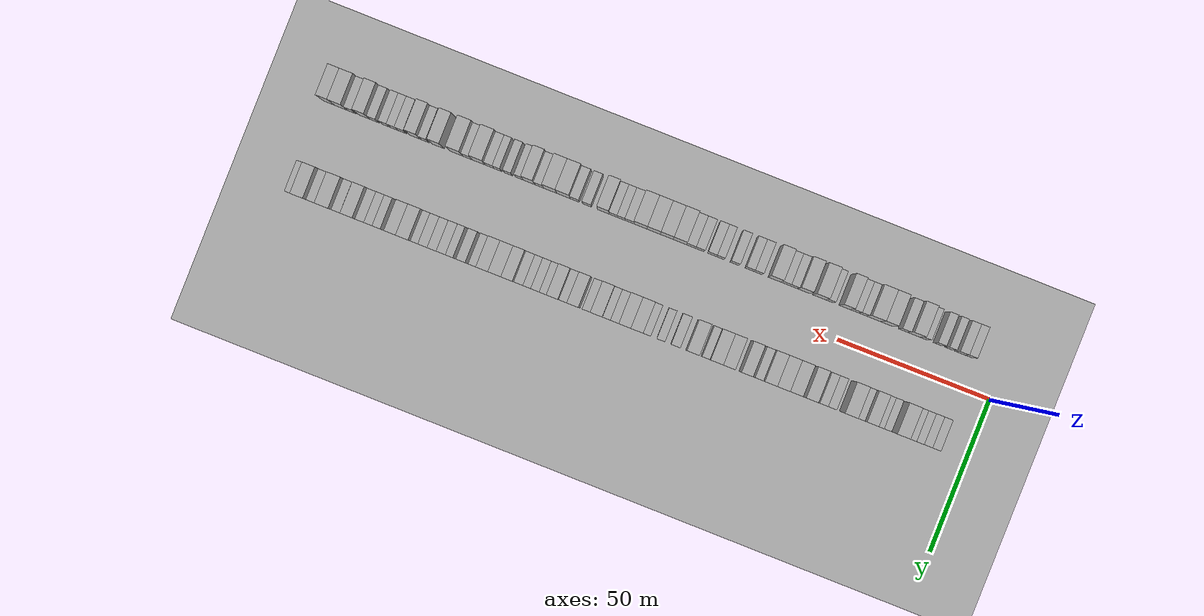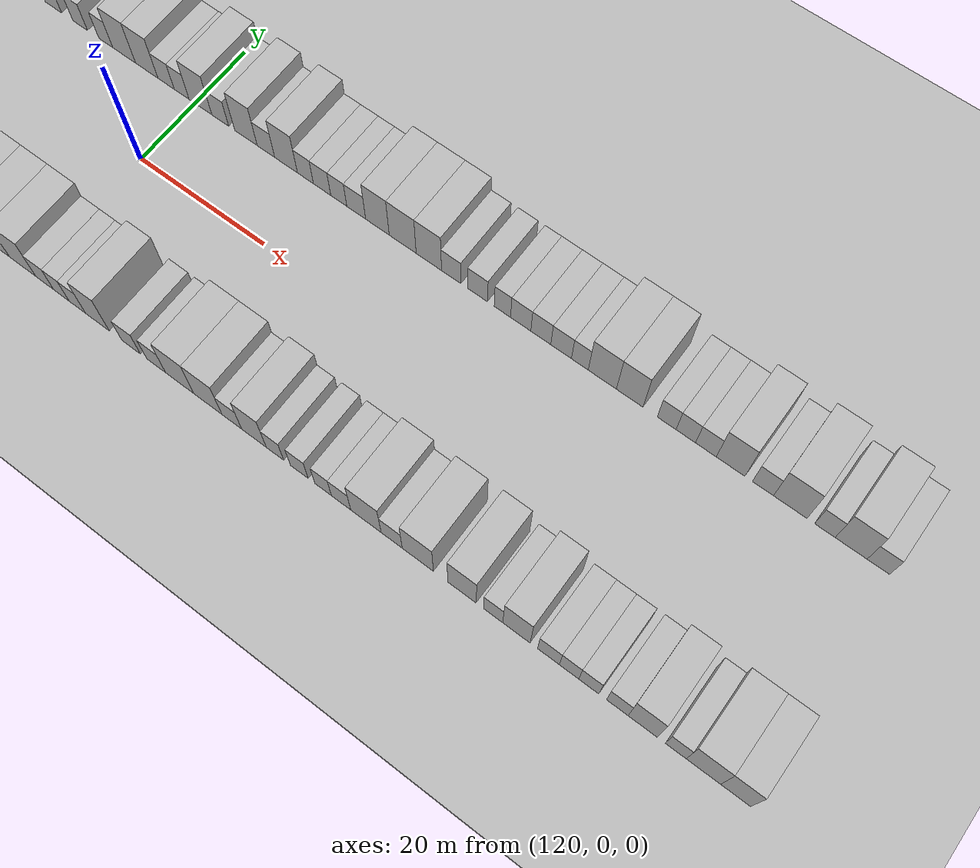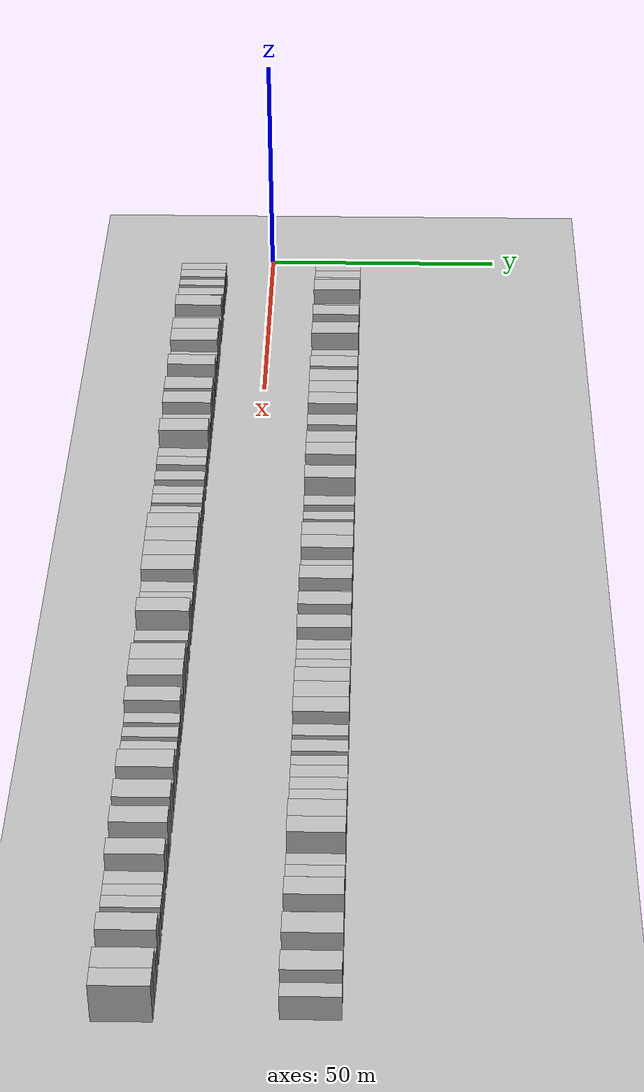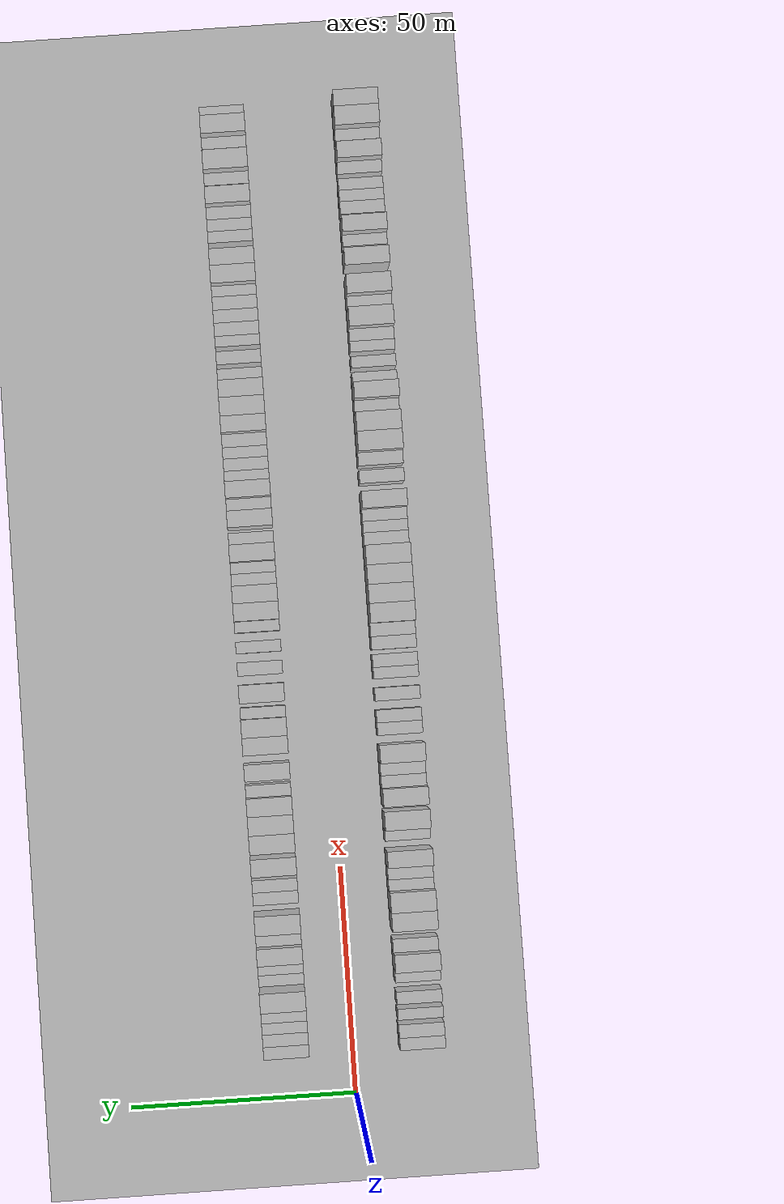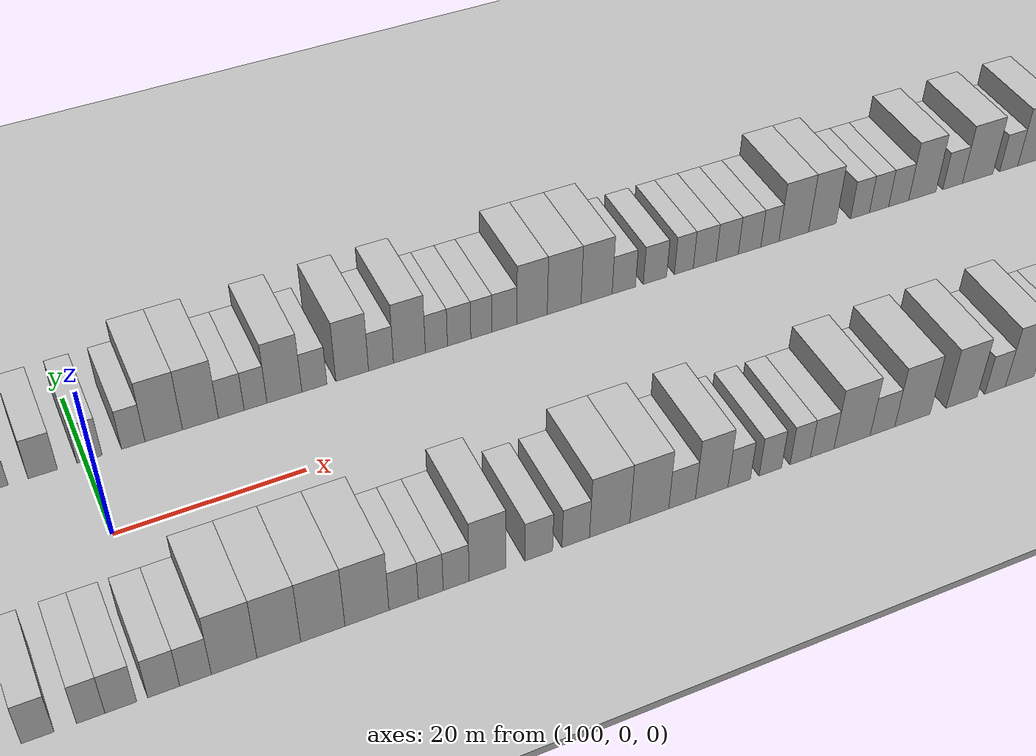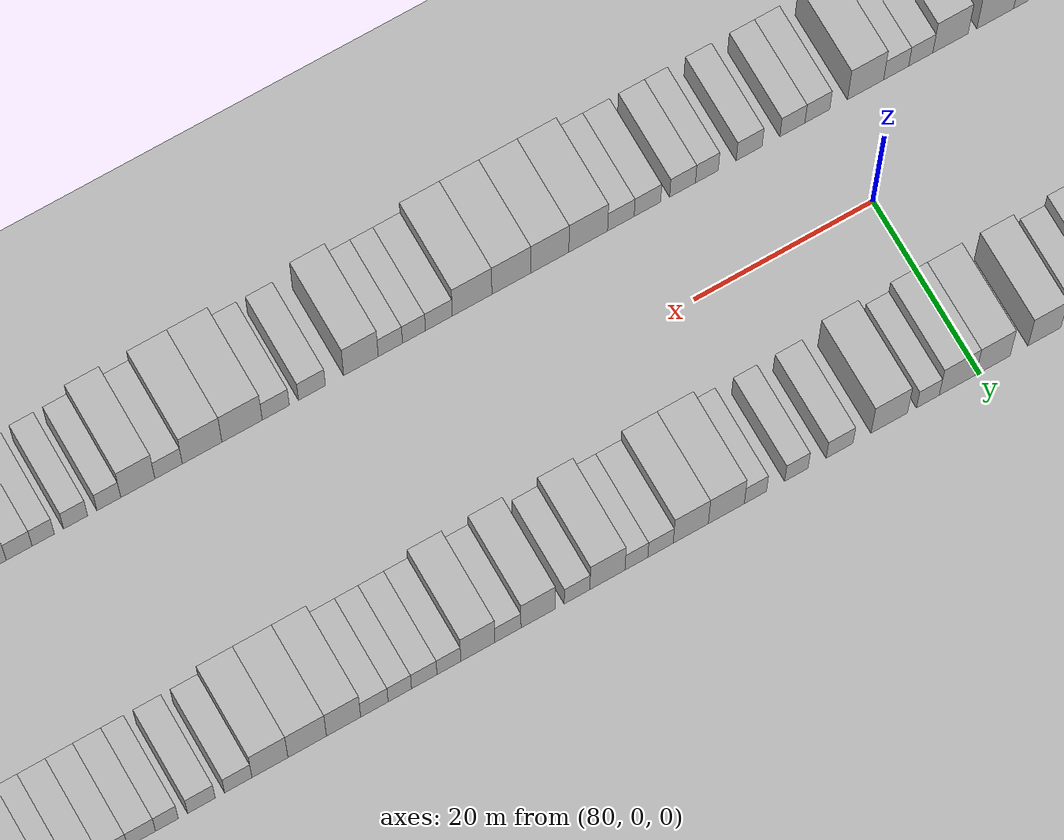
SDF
<?xml version="1.0" encoding="utf-8"?>

<sdf version="1.6">

   <world name="default">

      <gui fullscreen="0">

         <camera name="user_camera">

            <pose>-15 0 4.57585 0 0 0</pose>

            <view_controller>orbit</view_controller>

         </camera>

      </gui>

      <scene>

         <sky>

           <clouds>

             <speed>12</speed>

           </clouds>

         </sky>

         <ambient>0.4 0.4 0.4 1</ambient>

         <background>0.7 0.7 0.7 1</background>

         <shadows>1</shadows>

      </scene>

      <gravity>0 0 -9.8066</gravity>

      <magnetic_field>6e-06 2.3e-05 -4.2e-05</magnetic_field>

      <physics default="0" name="default_physics" type="ode">

         <ode>

            <solver>

               <type>quick</type>

               <iters>10</iters>

               <sor>1.0</sor>

               <use_dynamic_moi_rescaling>0</use_dynamic_moi_rescaling>

            </solver>

            <constraints>

               <cfm>0</cfm>

               <erp>0.2</erp>

               <contact_max_correcting_vel>100</contact_max_correcting_vel>

               <contact_surface_layer>0.001</contact_surface_layer>

            </constraints>

         </ode>

         <max_step_size>0.004</max_step_size>

         <real_time_factor>1</real_time_factor>

         <real_time_update_rate>250</real_time_update_rate>

      </physics>

      <light name="sun" type="directional">

         <cast_shadows>1</cast_shadows>

         <pose>0 0 10 0 0 0</pose>

         <diffuse>0.8 0.8 0.8 1</diffuse>

         <specular>0.2 0.2 0.2 1</specular>

         <attenuation>

            <range>1000</range>

            <constant>0.9</constant>

            <linear>0.01</linear>

            <quadratic>0.001</quadratic>

         </attenuation>

         <direction>-0.5 0.1 -0.9</direction>

      </light>

      <include>

         <name>ground_plane_1</name>

         <uri>model://HANNAS_ground_plane</uri>

         <pose>0 0 0  0 0 0</pose>

      </include>

      <include>

         <name>ground_plane_2</name>

         <uri>model://HANNAS_ground_plane</uri>

         <pose>100 0 0  0 0 0</pose>

      </include>

      <model name="building_1">

         <static>1</static>

         <pose frame="">11.3598 15.0000 0 0.000000 0.000000 1.570796</pose>

         <link name="link">

            <pose frame="">0 0 3.00 0 0 0</pose>

            <collision name="collision">

               <geometry>

                  <box>

                     <size>10.0000 2.7196 6.0000</size>

                  </box>

               </geometry>

               <max_contacts>10</max_contacts>

               <surface>

                  <contact>

                     <ode/>

                  </contact>

                  <bounce/>

                  <friction>

                     <torsional>

                        <ode/>

                     </torsional>

                     <ode/>

                  </friction>

               </surface>

            </collision>

            <visual name="visual">

               <cast_shadows>0</cast_shadows>

               <geometry>

                  <box>

                     <size>10.0000 2.7196 6.0000</size>

                  </box>

               </geometry>

               <material>

                  <script>

                     <uri>model://HANNAS_wall/materials/scripts</uri>

                     <uri>model://HANNAS_wall/materials/textures</uri>

                     <name>vrc/HANNAS_wall</name>

                  </script>

               </material>

            </visual>

            <self_collide>0</self_collide>

            <enable_wind>0</enable_wind>

            <kinematic>0</kinematic>

         </link>

      </model>

      <model name="building_2">

         <static>1</static>

         <pose frame="">14.0683 15.0000 0 0.000000 0.000000 1.570796</pose>

         <link name="link">

            <pose frame="">0 0 3.00 0 0 0</pose>

            <collision name="collision">

               <geometry>

                  <box>

                     <size>10.0000 2.6974 6.0000</size>

                  </box>

               </geometry>

               <max_contacts>10</max_contacts>

               <surface>

                  <contact>

                     <ode/>

                  </contact>

                  <bounce/>

                  <friction>

                     <torsional>

                        <ode/>

                     </torsional>

                     <ode/>

                  </friction>

               </surface>

            </collision>

            <visual name="visual">

               <cast_shadows>0</cast_shadows>

               <geometry>

                  <box>

                     <size>10.0000 2.6974 6.0000</size>

                  </box>

               </geometry>

               <material>

                  <script>

                     <uri>model://HANNAS_wall/materials/scripts</uri>

                     <uri>model://HANNAS_wall/materials/textures</uri>

                     <name>vrc/HANNAS_wall</name>

                  </script>

               </material>

            </visual>

            <self_collide>0</self_collide>

            <enable_wind>0</enable_wind>

            <kinematic>0</kinematic>

         </link>

      </model>

      <model name="building_3">

         <static>1</static>

         <pose frame="">16.6501 15.0000 0 0.000000 0.000000 1.570796</pose>

         <link name="link">

            <pose frame="">0 0 3.00 0 0 0</pose>

            <collision name="collision">

               <geometry>

                  <box>

                     <size>10.0000 2.4661 6.0000</size>

                  </box>

               </geometry>

               <max_contacts>10</max_contacts>

               <surface>

                  <contact>

                     <ode/>

                  </contact>

                  <bounce/>

                  <friction>

                     <torsional>

                        <ode/>

                     </torsional>

                     <ode/>

                  </friction>

               </surface>

            </collision>

            <visual name="visual">

               <cast_shadows>0</cast_shadows>

               <geometry>

                  <box>

                     <size>10.0000 2.4661 6.0000</size>

                  </box>

               </geometry>

               <material>

                  <script>

                     <uri>model://HANNAS_wall/materials/scripts</uri>

                     <uri>model://HANNAS_wall/materials/textures</uri>

                     <name>vrc/HANNAS_wall</name>

                  </script>

               </material>

            </visual>

            <self_collide>0</self_collide>

            <enable_wind>0</enable_wind>

            <kinematic>0</kinematic>

         </link>

      </model>

      <model name="building_4">

         <static>1</static>

         <pose frame="">19.2767 15.0000 0 0.000000 0.000000 1.570796</pose>

         <link name="link">

            <pose frame="">0 0 3.00 0 0 0</pose>

            <collision name="collision">

               <geometry>

                  <box>

                     <size>10.0000 2.7872 6.0000</size>

                  </box>

               </geometry>

               <max_contacts>10</max_contacts>

               <surface>

                  <contact>

                     <ode/>

                  </contact>

                  <bounce/>

                  <friction>

                     <torsional>

                        <ode/>

                     </torsional>

                     <ode/>

                  </friction>

               </surface>

            </collision>

            <visual name="visual">

               <cast_shadows>0</cast_shadows>

               <geometry>

                  <box>

                     <size>10.0000 2.7872 6.0000</size>

                  </box>

               </geometry>

               <material>

                  <script>

                     <uri>model://HANNAS_wall/materials/scripts</uri>

                     <uri>model://HANNAS_wall/materials/textures</uri>

                     <name>vrc/HANNAS_wall</name>

                  </script>

               </material>

            </visual>

            <self_collide>0</self_collide>

            <enable_wind>0</enable_wind>

            <kinematic>0</kinematic>

         </link>

      </model>

      <model name="building_5">

         <static>1</static>

         <pose frame="">22.7889 15.0000 0 0.000000 0.000000 1.570796</pose>

         <link name="link">

            <pose frame="">0 0 4.50 0 0 0</pose>

            <collision name="collision">

               <geometry>

                  <box>

                     <size>10.0000 4.2372 9.0000</size>

                  </box>

               </geometry>

               <max_contacts>10</max_contacts>

               <surface>

                  <contact>

                     <ode/>

                  </contact>

                  <bounce/>

                  <friction>

                     <torsional>

                        <ode/>

                     </torsional>

                     <ode/>

                  </friction>

               </surface>

            </collision>

            <visual name="visual">

               <cast_shadows>0</cast_shadows>

               <geometry>

                  <box>

                     <size>10.0000 4.2372 9.0000</size>

                  </box>

               </geometry>

               <material>

                  <script>

                     <uri>model://HANNAS_wall/materials/scripts</uri>

                     <uri>model://HANNAS_wall/materials/textures</uri>

                     <name>vrc/HANNAS_wall</name>

                  </script>

               </material>

            </visual>

            <self_collide>0</self_collide>

            <enable_wind>0</enable_wind>

            <kinematic>0</kinematic>

         </link>

      </model>

      <model name="building_6">

         <static>1</static>

         <pose frame="">27.1172 15.0000 0 0.000000 0.000000 1.570796</pose>

         <link name="link">

            <pose frame="">0 0 3.00 0 0 0</pose>

            <collision name="collision">

               <geometry>

                  <box>

                     <size>10.0000 2.4193 6.0000</size>

                  </box>

               </geometry>

               <max_contacts>10</max_contacts>

               <surface>

                  <contact>

                     <ode/>

                  </contact>

                  <bounce/>

                  <friction>

                     <torsional>

                        <ode/>

                     </torsional>

                     <ode/>

                  </friction>

               </surface>

            </collision>

            <visual name="visual">

               <cast_shadows>0</cast_shadows>

               <geometry>

                  <box>

                     <size>10.0000 2.4193 6.0000</size>

                  </box>

               </geometry>

               <material>

                  <script>

                     <uri>model://HANNAS_wall/materials/scripts</uri>

                     <uri>model://HANNAS_wall/materials/textures</uri>

                     <name>vrc/HANNAS_wall</name>

                  </script>

               </material>

            </visual>

            <self_collide>0</self_collide>

            <enable_wind>0</enable_wind>

            <kinematic>0</kinematic>

         </link>

      </model>

      <model name="building_7">

         <static>1</static>

         <pose frame="">29.5809 15.0000 0 0.000000 0.000000 1.570796</pose>

         <link name="link">

            <pose frame="">0 0 3.00 0 0 0</pose>

            <collision name="collision">

               <geometry>

                  <box>

                     <size>10.0000 2.5081 6.0000</size>

                  </box>

               </geometry>

               <max_contacts>10</max_contacts>

               <surface>

                  <contact>

                     <ode/>

                  </contact>

                  <bounce/>

                  <friction>

                     <torsional>

                        <ode/>

                     </torsional>

                     <ode/>

                  </friction>

               </surface>

            </collision>

            <visual name="visual">

               <cast_shadows>0</cast_shadows>

               <geometry>

                  <box>

                     <size>10.0000 2.5081 6.0000</size>

                  </box>

               </geometry>

               <material>

                  <script>

                     <uri>model://HANNAS_wall/materials/scripts</uri>

                     <uri>model://HANNAS_wall/materials/textures</uri>

                     <name>vrc/HANNAS_wall</name>

                  </script>

               </material>

            </visual>

            <self_collide>0</self_collide>

            <enable_wind>0</enable_wind>

            <kinematic>0</kinematic>

         </link>

      </model>

      <model name="building_8">

         <static>1</static>

         <pose frame="">32.6991 15.0000 0 0.000000 0.000000 1.570796</pose>

         <link name="link">

            <pose frame="">0 0 4.50 0 0 0</pose>

            <collision name="collision">

               <geometry>

                  <box>

                     <size>10.0000 3.7283 9.0000</size>

                  </box>

               </geometry>

               <max_contacts>10</max_contacts>

               <surface>

                  <contact>

                     <ode/>

                  </contact>

                  <bounce/>

                  <friction>

                     <torsional>

                        <ode/>

                     </torsional>

                     <ode/>

                  </friction>

               </surface>

            </collision>

            <visual name="visual">

               <cast_shadows>0</cast_shadows>

               <geometry>

                  <box>

                     <size>10.0000 3.7283 9.0000</size>

                  </box>

               </geometry>

               <material>

                  <script>

                     <uri>model://HANNAS_wall/materials/scripts</uri>

                     <uri>model://HANNAS_wall/materials/textures</uri>

                     <name>vrc/HANNAS_wall</name>

                  </script>

               </material>

            </visual>

            <self_collide>0</self_collide>

            <enable_wind>0</enable_wind>

            <kinematic>0</kinematic>

         </link>

      </model>

      <model name="building_9">

         <static>1</static>

         <pose frame="">35.9825 15.0000 0 0.000000 0.000000 1.570796</pose>

         <link name="link">

            <pose frame="">0 0 3.00 0 0 0</pose>

            <collision name="collision">

               <geometry>

                  <box>

                     <size>10.0000 2.8385 6.0000</size>

                  </box>

               </geometry>

               <max_contacts>10</max_contacts>

               <surface>

                  <contact>

                     <ode/>

                  </contact>

                  <bounce/>

                  <friction>

                     <torsional>

                        <ode/>

                     </torsional>

                     <ode/>

                  </friction>

               </surface>

            </collision>

            <visual name="visual">

               <cast_shadows>0</cast_shadows>

               <geometry>

                  <box>

                     <size>10.0000 2.8385 6.0000</size>

                  </box>

               </geometry>

               <material>

                  <script>

                     <uri>model://HANNAS_wall/materials/scripts</uri>

                     <uri>model://HANNAS_wall/materials/textures</uri>

                     <name>vrc/HANNAS_wall</name>

                  </script>

               </material>

            </visual>

            <self_collide>0</self_collide>

            <enable_wind>0</enable_wind>

            <kinematic>0</kinematic>

         </link>

      </model>

      <model name="building_10">

         <static>1</static>

         <pose frame="">39.5182 15.0000 0 0.000000 0.000000 1.570796</pose>

         <link name="link">

            <pose frame="">0 0 4.50 0 0 0</pose>

            <collision name="collision">

               <geometry>

                  <box>

                     <size>10.0000 4.2330 9.0000</size>

                  </box>

               </geometry>

               <max_contacts>10</max_contacts>

               <surface>

                  <contact>

                     <ode/>

                  </contact>

                  <bounce/>

                  <friction>

                     <torsional>

                        <ode/>

                     </torsional>

                     <ode/>

                  </friction>

               </surface>

            </collision>

            <visual name="visual">

               <cast_shadows>0</cast_shadows>

               <geometry>

                  <box>

                     <size>10.0000 4.2330 9.0000</size>

                  </box>

               </geometry>

               <material>

                  <script>

                     <uri>model://HANNAS_wall/materials/scripts</uri>

                     <uri>model://HANNAS_wall/materials/textures</uri>

                     <name>vrc/HANNAS_wall</name>

                  </script>

               </material>

            </visual>

            <self_collide>0</self_collide>

            <enable_wind>0</enable_wind>

            <kinematic>0</kinematic>

         </link>

      </model>

      <model name="building_11">

         <static>1</static>

         <pose frame="">45.0125 15.0000 0 0.000000 0.000000 1.570796</pose>

         <link name="link">

            <pose frame="">0 0 3.00 0 0 0</pose>

            <collision name="collision">

               <geometry>

                  <box>

                     <size>10.0000 2.7556 6.0000</size>

                  </box>

               </geometry>

               <max_contacts>10</max_contacts>

               <surface>

                  <contact>

                     <ode/>

                  </contact>

                  <bounce/>

                  <friction>

                     <torsional>

                        <ode/>

                     </torsional>

                     <ode/>

                  </friction>

               </surface>

            </collision>

            <visual name="visual">

               <cast_shadows>0</cast_shadows>

               <geometry>

                  <box>

                     <size>10.0000 2.7556 6.0000</size>

                  </box>

               </geometry>

               <material>

                  <script>

                     <uri>model://HANNAS_wall/materials/scripts</uri>

                     <uri>model://HANNAS_wall/materials/textures</uri>

                     <name>vrc/HANNAS_wall</name>

                  </script>

               </material>

            </visual>

            <self_collide>0</self_collide>

            <enable_wind>0</enable_wind>

            <kinematic>0</kinematic>

         </link>

      </model>

      <model name="building_12">

         <static>1</static>

         <pose frame="">47.7491 15.0000 0 0.000000 0.000000 1.570796</pose>

         <link name="link">

            <pose frame="">0 0 3.00 0 0 0</pose>

            <collision name="collision">

               <geometry>

                  <box>

                     <size>10.0000 2.7178 6.0000</size>

                  </box>

               </geometry>

               <max_contacts>10</max_contacts>

               <surface>

                  <contact>

                     <ode/>

                  </contact>

                  <bounce/>

                  <friction>

                     <torsional>

                        <ode/>

                     </torsional>

                     <ode/>

                  </friction>

               </surface>

            </collision>

            <visual name="visual">

               <cast_shadows>0</cast_shadows>

               <geometry>

                  <box>

                     <size>10.0000 2.7178 6.0000</size>

                  </box>

               </geometry>

               <material>

                  <script>

                     <uri>model://HANNAS_wall/materials/scripts</uri>

                     <uri>model://HANNAS_wall/materials/textures</uri>

                     <name>vrc/HANNAS_wall</name>

                  </script>

               </material>

            </visual>

            <self_collide>0</self_collide>

            <enable_wind>0</enable_wind>

            <kinematic>0</kinematic>

         </link>

      </model>

      <model name="building_13">

         <static>1</static>

         <pose frame="">52.0646 15.0000 0 0.000000 0.000000 1.570796</pose>

         <link name="link">

            <pose frame="">0 0 4.50 0 0 0</pose>

            <collision name="collision">

               <geometry>

                  <box>

                     <size>10.0000 3.9132 9.0000</size>

                  </box>

               </geometry>

               <max_contacts>10</max_contacts>

               <surface>

                  <contact>

                     <ode/>

                  </contact>

                  <bounce/>

                  <friction>

                     <torsional>

                        <ode/>

                     </torsional>

                     <ode/>

                  </friction>

               </surface>

            </collision>

            <visual name="visual">

               <cast_shadows>0</cast_shadows>

               <geometry>

                  <box>

                     <size>10.0000 3.9132 9.0000</size>

                  </box>

               </geometry>

               <material>

                  <script>

                     <uri>model://HANNAS_wall/materials/scripts</uri>

                     <uri>model://HANNAS_wall/materials/textures</uri>

                     <name>vrc/HANNAS_wall</name>

                  </script>

               </material>

            </visual>

            <self_collide>0</self_collide>

            <enable_wind>0</enable_wind>

            <kinematic>0</kinematic>

         </link>

      </model>

      <model name="building_14">

         <static>1</static>

         <pose frame="">57.0853 15.0000 0 0.000000 0.000000 1.570796</pose>

         <link name="link">

            <pose frame="">0 0 4.50 0 0 0</pose>

            <collision name="collision">

               <geometry>

                  <box>

                     <size>10.0000 4.1283 9.0000</size>

                  </box>

               </geometry>

               <max_contacts>10</max_contacts>

               <surface>

                  <contact>

                     <ode/>

                  </contact>

                  <bounce/>

                  <friction>

                     <torsional>

                        <ode/>

                     </torsional>

                     <ode/>

                  </friction>

               </surface>

            </collision>

            <visual name="visual">

               <cast_shadows>0</cast_shadows>

               <geometry>

                  <box>

                     <size>10.0000 4.1283 9.0000</size>

                  </box>

               </geometry>

               <material>

                  <script>

                     <uri>model://HANNAS_wall/materials/scripts</uri>

                     <uri>model://HANNAS_wall/materials/textures</uri>

                     <name>vrc/HANNAS_wall</name>

                  </script>

               </material>

            </visual>

            <self_collide>0</self_collide>

            <enable_wind>0</enable_wind>

            <kinematic>0</kinematic>

         </link>

      </model>

      <model name="building_15">

         <static>1</static>

         <pose frame="">61.2078 15.0000 0 0.000000 0.000000 1.570796</pose>

         <link name="link">

            <pose frame="">0 0 4.50 0 0 0</pose>

            <collision name="collision">

               <geometry>

                  <box>

                     <size>10.0000 4.1166 9.0000</size>

                  </box>

               </geometry>

               <max_contacts>10</max_contacts>

               <surface>

                  <contact>

                     <ode/>

                  </contact>

                  <bounce/>

                  <friction>

                     <torsional>

                        <ode/>

                     </torsional>

                     <ode/>

                  </friction>

               </surface>

            </collision>

            <visual name="visual">

               <cast_shadows>0</cast_shadows>

               <geometry>

                  <box>

                     <size>10.0000 4.1166 9.0000</size>

                  </box>

               </geometry>

               <material>

                  <script>

                     <uri>model://HANNAS_wall/materials/scripts</uri>

                     <uri>model://HANNAS_wall/materials/textures</uri>

                     <name>vrc/HANNAS_wall</name>

                  </script>

               </material>

            </visual>

            <self_collide>0</self_collide>

            <enable_wind>0</enable_wind>

            <kinematic>0</kinematic>

         </link>

      </model>

      <model name="building_16">

         <static>1</static>

         <pose frame="">65.2668 15.0000 0 0.000000 0.000000 1.570796</pose>

         <link name="link">

            <pose frame="">0 0 4.50 0 0 0</pose>

            <collision name="collision">

               <geometry>

                  <box>

                     <size>10.0000 4.0015 9.0000</size>

                  </box>

               </geometry>

               <max_contacts>10</max_contacts>

               <surface>

                  <contact>

                     <ode/>

                  </contact>

                  <bounce/>

                  <friction>

                     <torsional>

                        <ode/>

                     </torsional>

                     <ode/>

                  </friction>

               </surface>

            </collision>

            <visual name="visual">

               <cast_shadows>0</cast_shadows>

               <geometry>

                  <box>

                     <size>10.0000 4.0015 9.0000</size>

                  </box>

               </geometry>

               <material>

                  <script>

                     <uri>model://HANNAS_wall/materials/scripts</uri>

                     <uri>model://HANNAS_wall/materials/textures</uri>

                     <name>vrc/HANNAS_wall</name>

                  </script>

               </material>

            </visual>

            <self_collide>0</self_collide>

            <enable_wind>0</enable_wind>

            <kinematic>0</kinematic>

         </link>

      </model>

      <model name="building_17">

         <static>1</static>

         <pose frame="">68.6369 15.0000 0 0.000000 0.000000 1.570796</pose>

         <link name="link">

            <pose frame="">0 0 3.00 0 0 0</pose>

            <collision name="collision">

               <geometry>

                  <box>

                     <size>10.0000 2.7386 6.0000</size>

                  </box>

               </geometry>

               <max_contacts>10</max_contacts>

               <surface>

                  <contact>

                     <ode/>

                  </contact>

                  <bounce/>

                  <friction>

                     <torsional>

                        <ode/>

                     </torsional>

                     <ode/>

                  </friction>

               </surface>

            </collision>

            <visual name="visual">

               <cast_shadows>0</cast_shadows>

               <geometry>

                  <box>

                     <size>10.0000 2.7386 6.0000</size>

                  </box>

               </geometry>

               <material>

                  <script>

                     <uri>model://HANNAS_wall/materials/scripts</uri>

                     <uri>model://HANNAS_wall/materials/textures</uri>

                     <name>vrc/HANNAS_wall</name>

                  </script>

               </material>

            </visual>

            <self_collide>0</self_collide>

            <enable_wind>0</enable_wind>

            <kinematic>0</kinematic>

         </link>

      </model>

      <model name="building_18">

         <static>1</static>

         <pose frame="">72.8464 15.0000 0 0.000000 0.000000 1.570796</pose>

         <link name="link">

            <pose frame="">0 0 4.50 0 0 0</pose>

            <collision name="collision">

               <geometry>

                  <box>

                     <size>10.0000 3.6804 9.0000</size>

                  </box>

               </geometry>

               <max_contacts>10</max_contacts>

               <surface>

                  <contact>

                     <ode/>

                  </contact>

                  <bounce/>

                  <friction>

                     <torsional>

                        <ode/>

                     </torsional>

                     <ode/>

                  </friction>

               </surface>

            </collision>

            <visual name="visual">

               <cast_shadows>0</cast_shadows>

               <geometry>

                  <box>

                     <size>10.0000 3.6804 9.0000</size>

                  </box>

               </geometry>

               <material>

                  <script>

                     <uri>model://HANNAS_wall/materials/scripts</uri>

                     <uri>model://HANNAS_wall/materials/textures</uri>

                     <name>vrc/HANNAS_wall</name>

                  </script>

               </material>

            </visual>

            <self_collide>0</self_collide>

            <enable_wind>0</enable_wind>

            <kinematic>0</kinematic>

         </link>

      </model>

      <model name="building_19">

         <static>1</static>

         <pose frame="">78.6091 15.0000 0 0.000000 0.000000 1.570796</pose>

         <link name="link">

            <pose frame="">0 0 4.50 0 0 0</pose>

            <collision name="collision">

               <geometry>

                  <box>

                     <size>10.0000 3.8452 9.0000</size>

                  </box>

               </geometry>

               <max_contacts>10</max_contacts>

               <surface>

                  <contact>

                     <ode/>

                  </contact>

                  <bounce/>

                  <friction>

                     <torsional>

                        <ode/>

                     </torsional>

                     <ode/>

                  </friction>

               </surface>

            </collision>

            <visual name="visual">

               <cast_shadows>0</cast_shadows>

               <geometry>

                  <box>

                     <size>10.0000 3.8452 9.0000</size>

                  </box>

               </geometry>

               <material>

                  <script>

                     <uri>model://HANNAS_wall/materials/scripts</uri>

                     <uri>model://HANNAS_wall/materials/textures</uri>

                     <name>vrc/HANNAS_wall</name>

                  </script>

               </material>

            </visual>

            <self_collide>0</self_collide>

            <enable_wind>0</enable_wind>

            <kinematic>0</kinematic>

         </link>

      </model>

      <model name="building_20">

         <static>1</static>

         <pose frame="">82.5596 15.0000 0 0.000000 0.000000 1.570796</pose>

         <link name="link">

            <pose frame="">0 0 4.50 0 0 0</pose>

            <collision name="collision">

               <geometry>

                  <box>

                     <size>10.0000 4.0557 9.0000</size>

                  </box>

               </geometry>

               <max_contacts>10</max_contacts>

               <surface>

                  <contact>

                     <ode/>

                  </contact>

                  <bounce/>

                  <friction>

                     <torsional>

                        <ode/>

                     </torsional>

                     <ode/>

                  </friction>

               </surface>

            </collision>

            <visual name="visual">

               <cast_shadows>0</cast_shadows>

               <geometry>

                  <box>

                     <size>10.0000 4.0557 9.0000</size>

                  </box>

               </geometry>

               <material>

                  <script>

                     <uri>model://HANNAS_wall/materials/scripts</uri>

                     <uri>model://HANNAS_wall/materials/textures</uri>

                     <name>vrc/HANNAS_wall</name>

                  </script>

               </material>

            </visual>

            <self_collide>0</self_collide>

            <enable_wind>0</enable_wind>

            <kinematic>0</kinematic>

         </link>

      </model>

      <model name="building_21">

         <static>1</static>

         <pose frame="">85.8498 15.0000 0 0.000000 0.000000 1.570796</pose>

         <link name="link">

            <pose frame="">0 0 3.00 0 0 0</pose>

            <collision name="collision">

               <geometry>

                  <box>

                     <size>10.0000 2.5248 6.0000</size>

                  </box>

               </geometry>

               <max_contacts>10</max_contacts>

               <surface>

                  <contact>

                     <ode/>

                  </contact>

                  <bounce/>

                  <friction>

                     <torsional>

                        <ode/>

                     </torsional>

                     <ode/>

                  </friction>

               </surface>

            </collision>

            <visual name="visual">

               <cast_shadows>0</cast_shadows>

               <geometry>

                  <box>

                     <size>10.0000 2.5248 6.0000</size>

                  </box>

               </geometry>

               <material>

                  <script>

                     <uri>model://HANNAS_wall/materials/scripts</uri>

                     <uri>model://HANNAS_wall/materials/textures</uri>

                     <name>vrc/HANNAS_wall</name>

                  </script>

               </material>

            </visual>

            <self_collide>0</self_collide>

            <enable_wind>0</enable_wind>

            <kinematic>0</kinematic>

         </link>

      </model>

      <model name="building_22">

         <static>1</static>

         <pose frame="">90.1329 15.0000 0 0.000000 0.000000 1.570796</pose>

         <link name="link">

            <pose frame="">0 0 4.50 0 0 0</pose>

            <collision name="collision">

               <geometry>

                  <box>

                     <size>10.0000 4.0415 9.0000</size>

                  </box>

               </geometry>

               <max_contacts>10</max_contacts>

               <surface>

                  <contact>

                     <ode/>

                  </contact>

                  <bounce/>

                  <friction>

                     <torsional>

                        <ode/>

                     </torsional>

                     <ode/>

                  </friction>

               </surface>

            </collision>

            <visual name="visual">

               <cast_shadows>0</cast_shadows>

               <geometry>

                  <box>

                     <size>10.0000 4.0415 9.0000</size>

                  </box>

               </geometry>

               <material>

                  <script>

                     <uri>model://HANNAS_wall/materials/scripts</uri>

                     <uri>model://HANNAS_wall/materials/textures</uri>

                     <name>vrc/HANNAS_wall</name>

                  </script>

               </material>

            </visual>

            <self_collide>0</self_collide>

            <enable_wind>0</enable_wind>

            <kinematic>0</kinematic>

         </link>

      </model>

      <model name="building_23">

         <static>1</static>

         <pose frame="">95.6422 15.0000 0 0.000000 0.000000 1.570796</pose>

         <link name="link">

            <pose frame="">0 0 3.00 0 0 0</pose>

            <collision name="collision">

               <geometry>

                  <box>

                     <size>10.0000 2.9771 6.0000</size>

                  </box>

               </geometry>

               <max_contacts>10</max_contacts>

               <surface>

                  <contact>

                     <ode/>

                  </contact>

                  <bounce/>

                  <friction>

                     <torsional>

                        <ode/>

                     </torsional>

                     <ode/>

                  </friction>

               </surface>

            </collision>

            <visual name="visual">

               <cast_shadows>0</cast_shadows>

               <geometry>

                  <box>

                     <size>10.0000 2.9771 6.0000</size>

                  </box>

               </geometry>

               <material>

                  <script>

                     <uri>model://HANNAS_wall/materials/scripts</uri>

                     <uri>model://HANNAS_wall/materials/textures</uri>

                     <name>vrc/HANNAS_wall</name>

                  </script>

               </material>

            </visual>

            <self_collide>0</self_collide>

            <enable_wind>0</enable_wind>

            <kinematic>0</kinematic>

         </link>

      </model>

      <model name="building_24">

         <static>1</static>

         <pose frame="">100.4237 15.0000 0 0.000000 0.000000 1.570796</pose>

         <link name="link">

            <pose frame="">0 0 3.00 0 0 0</pose>

            <collision name="collision">

               <geometry>

                  <box>

                     <size>10.0000 2.5860 6.0000</size>

                  </box>

               </geometry>

               <max_contacts>10</max_contacts>

               <surface>

                  <contact>

                     <ode/>

                  </contact>

                  <bounce/>

                  <friction>

                     <torsional>

                        <ode/>

                     </torsional>

                     <ode/>

                  </friction>

               </surface>

            </collision>

            <visual name="visual">

               <cast_shadows>0</cast_shadows>

               <geometry>

                  <box>

                     <size>10.0000 2.5860 6.0000</size>

                  </box>

               </geometry>

               <material>

                  <script>

                     <uri>model://HANNAS_wall/materials/scripts</uri>

                     <uri>model://HANNAS_wall/materials/textures</uri>

                     <name>vrc/HANNAS_wall</name>

                  </script>

               </material>

            </visual>

            <self_collide>0</self_collide>

            <enable_wind>0</enable_wind>

            <kinematic>0</kinematic>

         </link>

      </model>

      <model name="building_25">

         <static>1</static>

         <pose frame="">104.9449 15.0000 0 0.000000 0.000000 1.570796</pose>

         <link name="link">

            <pose frame="">0 0 3.00 0 0 0</pose>

            <collision name="collision">

               <geometry>

                  <box>

                     <size>10.0000 2.4564 6.0000</size>

                  </box>

               </geometry>

               <max_contacts>10</max_contacts>

               <surface>

                  <contact>

                     <ode/>

                  </contact>

                  <bounce/>

                  <friction>

                     <torsional>

                        <ode/>

                     </torsional>

                     <ode/>

                  </friction>

               </surface>

            </collision>

            <visual name="visual">

               <cast_shadows>0</cast_shadows>

               <geometry>

                  <box>

                     <size>10.0000 2.4564 6.0000</size>

                  </box>

               </geometry>

               <material>

                  <script>

                     <uri>model://HANNAS_wall/materials/scripts</uri>

                     <uri>model://HANNAS_wall/materials/textures</uri>

                     <name>vrc/HANNAS_wall</name>

                  </script>

               </material>

            </visual>

            <self_collide>0</self_collide>

            <enable_wind>0</enable_wind>

            <kinematic>0</kinematic>

         </link>

      </model>

      <model name="building_26">

         <static>1</static>

         <pose frame="">108.1541 15.0000 0 0.000000 0.000000 1.570796</pose>

         <link name="link">

            <pose frame="">0 0 4.50 0 0 0</pose>

            <collision name="collision">

               <geometry>

                  <box>

                     <size>10.0000 3.9619 9.0000</size>

                  </box>

               </geometry>

               <max_contacts>10</max_contacts>

               <surface>

                  <contact>

                     <ode/>

                  </contact>

                  <bounce/>

                  <friction>

                     <torsional>

                        <ode/>

                     </torsional>

                     <ode/>

                  </friction>

               </surface>

            </collision>

            <visual name="visual">

               <cast_shadows>0</cast_shadows>

               <geometry>

                  <box>

                     <size>10.0000 3.9619 9.0000</size>

                  </box>

               </geometry>

               <material>

                  <script>

                     <uri>model://HANNAS_wall/materials/scripts</uri>

                     <uri>model://HANNAS_wall/materials/textures</uri>

                     <name>vrc/HANNAS_wall</name>

                  </script>

               </material>

            </visual>

            <self_collide>0</self_collide>

            <enable_wind>0</enable_wind>

            <kinematic>0</kinematic>

         </link>

      </model>

      <model name="building_27">

         <static>1</static>

         <pose frame="">112.0646 15.0000 0 0.000000 0.000000 1.570796</pose>

         <link name="link">

            <pose frame="">0 0 4.50 0 0 0</pose>

            <collision name="collision">

               <geometry>

                  <box>

                     <size>10.0000 3.8592 9.0000</size>

                  </box>

               </geometry>

               <max_contacts>10</max_contacts>

               <surface>

                  <contact>

                     <ode/>

                  </contact>

                  <bounce/>

                  <friction>

                     <torsional>

                        <ode/>

                     </torsional>

                     <ode/>

                  </friction>

               </surface>

            </collision>

            <visual name="visual">

               <cast_shadows>0</cast_shadows>

               <geometry>

                  <box>

                     <size>10.0000 3.8592 9.0000</size>

                  </box>

               </geometry>

               <material>

                  <script>

                     <uri>model://HANNAS_wall/materials/scripts</uri>

                     <uri>model://HANNAS_wall/materials/textures</uri>

                     <name>vrc/HANNAS_wall</name>

                  </script>

               </material>

            </visual>

            <self_collide>0</self_collide>

            <enable_wind>0</enable_wind>

            <kinematic>0</kinematic>

         </link>

      </model>

      <model name="building_28">

         <static>1</static>

         <pose frame="">115.3843 15.0000 0 0.000000 0.000000 1.570796</pose>

         <link name="link">

            <pose frame="">0 0 3.00 0 0 0</pose>

            <collision name="collision">

               <geometry>

                  <box>

                     <size>10.0000 2.7801 6.0000</size>

                  </box>

               </geometry>

               <max_contacts>10</max_contacts>

               <surface>

                  <contact>

                     <ode/>

                  </contact>

                  <bounce/>

                  <friction>

                     <torsional>

                        <ode/>

                     </torsional>

                     <ode/>

                  </friction>

               </surface>

            </collision>

            <visual name="visual">

               <cast_shadows>0</cast_shadows>

               <geometry>

                  <box>

                     <size>10.0000 2.7801 6.0000</size>

                  </box>

               </geometry>

               <material>

                  <script>

                     <uri>model://HANNAS_wall/materials/scripts</uri>

                     <uri>model://HANNAS_wall/materials/textures</uri>

                     <name>vrc/HANNAS_wall</name>

                  </script>

               </material>

            </visual>

            <self_collide>0</self_collide>

            <enable_wind>0</enable_wind>

            <kinematic>0</kinematic>

         </link>

      </model>

      <model name="building_29">

         <static>1</static>

         <pose frame="">118.0255 15.0000 0 0.000000 0.000000 1.570796</pose>

         <link name="link">

            <pose frame="">0 0 3.00 0 0 0</pose>

            <collision name="collision">

               <geometry>

                  <box>

                     <size>10.0000 2.5024 6.0000</size>

                  </box>

               </geometry>

               <max_contacts>10</max_contacts>

               <surface>

                  <contact>

                     <ode/>

                  </contact>

                  <bounce/>

                  <friction>

                     <torsional>

                        <ode/>

                     </torsional>

                     <ode/>

                  </friction>

               </surface>

            </collision>

            <visual name="visual">

               <cast_shadows>0</cast_shadows>

               <geometry>

                  <box>

                     <size>10.0000 2.5024 6.0000</size>

                  </box>

               </geometry>

               <material>

                  <script>

                     <uri>model://HANNAS_wall/materials/scripts</uri>

                     <uri>model://HANNAS_wall/materials/textures</uri>

                     <name>vrc/HANNAS_wall</name>

                  </script>

               </material>

            </visual>

            <self_collide>0</self_collide>

            <enable_wind>0</enable_wind>

            <kinematic>0</kinematic>

         </link>

      </model>

      <model name="building_30">

         <static>1</static>

         <pose frame="">121.2008 15.0000 0 0.000000 0.000000 1.570796</pose>

         <link name="link">

            <pose frame="">0 0 4.50 0 0 0</pose>

            <collision name="collision">

               <geometry>

                  <box>

                     <size>10.0000 3.8482 9.0000</size>

                  </box>

               </geometry>

               <max_contacts>10</max_contacts>

               <surface>

                  <contact>

                     <ode/>

                  </contact>

                  <bounce/>

                  <friction>

                     <torsional>

                        <ode/>

                     </torsional>

                     <ode/>

                  </friction>

               </surface>

            </collision>

            <visual name="visual">

               <cast_shadows>0</cast_shadows>

               <geometry>

                  <box>

                     <size>10.0000 3.8482 9.0000</size>

                  </box>

               </geometry>

               <material>

                  <script>

                     <uri>model://HANNAS_wall/materials/scripts</uri>

                     <uri>model://HANNAS_wall/materials/textures</uri>

                     <name>vrc/HANNAS_wall</name>

                  </script>

               </material>

            </visual>

            <self_collide>0</self_collide>

            <enable_wind>0</enable_wind>

            <kinematic>0</kinematic>

         </link>

      </model>

      <model name="building_31">

         <static>1</static>

         <pose frame="">124.5239 15.0000 0 0.000000 0.000000 1.570796</pose>

         <link name="link">

            <pose frame="">0 0 3.00 0 0 0</pose>

            <collision name="collision">

               <geometry>

                  <box>

                     <size>10.0000 2.7982 6.0000</size>

                  </box>

               </geometry>

               <max_contacts>10</max_contacts>

               <surface>

                  <contact>

                     <ode/>

                  </contact>

                  <bounce/>

                  <friction>

                     <torsional>

                        <ode/>

                     </torsional>

                     <ode/>

                  </friction>

               </surface>

            </collision>

            <visual name="visual">

               <cast_shadows>0</cast_shadows>

               <geometry>

                  <box>

                     <size>10.0000 2.7982 6.0000</size>

                  </box>

               </geometry>

               <material>

                  <script>

                     <uri>model://HANNAS_wall/materials/scripts</uri>

                     <uri>model://HANNAS_wall/materials/textures</uri>

                     <name>vrc/HANNAS_wall</name>

                  </script>

               </material>

            </visual>

            <self_collide>0</self_collide>

            <enable_wind>0</enable_wind>

            <kinematic>0</kinematic>

         </link>

      </model>

      <model name="building_32">

         <static>1</static>

         <pose frame="">128.7800 15.0000 0 0.000000 0.000000 1.570796</pose>

         <link name="link">

            <pose frame="">0 0 4.50 0 0 0</pose>

            <collision name="collision">

               <geometry>

                  <box>

                     <size>10.0000 3.7140 9.0000</size>

                  </box>

               </geometry>

               <max_contacts>10</max_contacts>

               <surface>

                  <contact>

                     <ode/>

                  </contact>

                  <bounce/>

                  <friction>

                     <torsional>

                        <ode/>

                     </torsional>

                     <ode/>

                  </friction>

               </surface>

            </collision>

            <visual name="visual">

               <cast_shadows>0</cast_shadows>

               <geometry>

                  <box>

                     <size>10.0000 3.7140 9.0000</size>

                  </box>

               </geometry>

               <material>

                  <script>

                     <uri>model://HANNAS_wall/materials/scripts</uri>

                     <uri>model://HANNAS_wall/materials/textures</uri>

                     <name>vrc/HANNAS_wall</name>

                  </script>

               </material>

            </visual>

            <self_collide>0</self_collide>

            <enable_wind>0</enable_wind>

            <kinematic>0</kinematic>

         </link>

      </model>

      <model name="building_33">

         <static>1</static>

         <pose frame="">132.0614 15.0000 0 0.000000 0.000000 1.570796</pose>

         <link name="link">

            <pose frame="">0 0 3.00 0 0 0</pose>

            <collision name="collision">

               <geometry>

                  <box>

                     <size>10.0000 2.8488 6.0000</size>

                  </box>

               </geometry>

               <max_contacts>10</max_contacts>

               <surface>

                  <contact>

                     <ode/>

                  </contact>

                  <bounce/>

                  <friction>

                     <torsional>

                        <ode/>

                     </torsional>

                     <ode/>

                  </friction>

               </surface>

            </collision>

            <visual name="visual">

               <cast_shadows>0</cast_shadows>

               <geometry>

                  <box>

                     <size>10.0000 2.8488 6.0000</size>

                  </box>

               </geometry>

               <material>

                  <script>

                     <uri>model://HANNAS_wall/materials/scripts</uri>

                     <uri>model://HANNAS_wall/materials/textures</uri>

                     <name>vrc/HANNAS_wall</name>

                  </script>

               </material>

            </visual>

            <self_collide>0</self_collide>

            <enable_wind>0</enable_wind>

            <kinematic>0</kinematic>

         </link>

      </model>

      <model name="building_34">

         <static>1</static>

         <pose frame="">135.3368 15.0000 0 0.000000 0.000000 1.570796</pose>

         <link name="link">

            <pose frame="">0 0 4.50 0 0 0</pose>

            <collision name="collision">

               <geometry>

                  <box>

                     <size>10.0000 3.7020 9.0000</size>

                  </box>

               </geometry>

               <max_contacts>10</max_contacts>

               <surface>

                  <contact>

                     <ode/>

                  </contact>

                  <bounce/>

                  <friction>

                     <torsional>

                        <ode/>

                     </torsional>

                     <ode/>

                  </friction>

               </surface>

            </collision>

            <visual name="visual">

               <cast_shadows>0</cast_shadows>

               <geometry>

                  <box>

                     <size>10.0000 3.7020 9.0000</size>

                  </box>

               </geometry>

               <material>

                  <script>

                     <uri>model://HANNAS_wall/materials/scripts</uri>

                     <uri>model://HANNAS_wall/materials/textures</uri>

                     <name>vrc/HANNAS_wall</name>

                  </script>

               </material>

            </visual>

            <self_collide>0</self_collide>

            <enable_wind>0</enable_wind>

            <kinematic>0</kinematic>

         </link>

      </model>

      <model name="building_35">

         <static>1</static>

         <pose frame="">138.4774 15.0000 0 0.000000 0.000000 1.570796</pose>

         <link name="link">

            <pose frame="">0 0 3.00 0 0 0</pose>

            <collision name="collision">

               <geometry>

                  <box>

                     <size>10.0000 2.5791 6.0000</size>

                  </box>

               </geometry>

               <max_contacts>10</max_contacts>

               <surface>

                  <contact>

                     <ode/>

                  </contact>

                  <bounce/>

                  <friction>

                     <torsional>

                        <ode/>

                     </torsional>

                     <ode/>

                  </friction>

               </surface>

            </collision>

            <visual name="visual">

               <cast_shadows>0</cast_shadows>

               <geometry>

                  <box>

                     <size>10.0000 2.5791 6.0000</size>

                  </box>

               </geometry>

               <material>

                  <script>

                     <uri>model://HANNAS_wall/materials/scripts</uri>

                     <uri>model://HANNAS_wall/materials/textures</uri>

                     <name>vrc/HANNAS_wall</name>

                  </script>

               </material>

            </visual>

            <self_collide>0</self_collide>

            <enable_wind>0</enable_wind>

            <kinematic>0</kinematic>

         </link>

      </model>

      <model name="building_36">

         <static>1</static>

         <pose frame="">141.1463 15.0000 0 0.000000 0.000000 1.570796</pose>

         <link name="link">

            <pose frame="">0 0 3.00 0 0 0</pose>

            <collision name="collision">

               <geometry>

                  <box>

                     <size>10.0000 2.7586 6.0000</size>

                  </box>

               </geometry>

               <max_contacts>10</max_contacts>

               <surface>

                  <contact>

                     <ode/>

                  </contact>

                  <bounce/>

                  <friction>

                     <torsional>

                        <ode/>

                     </torsional>

                     <ode/>

                  </friction>

               </surface>

            </collision>

            <visual name="visual">

               <cast_shadows>0</cast_shadows>

               <geometry>

                  <box>

                     <size>10.0000 2.7586 6.0000</size>

                  </box>

               </geometry>

               <material>

                  <script>

                     <uri>model://HANNAS_wall/materials/scripts</uri>

                     <uri>model://HANNAS_wall/materials/textures</uri>

                     <name>vrc/HANNAS_wall</name>

                  </script>

               </material>

            </visual>

            <self_collide>0</self_collide>

            <enable_wind>0</enable_wind>

            <kinematic>0</kinematic>

         </link>

      </model>

      <model name="building_37">

         <static>1</static>

         <pose frame="">143.7925 15.0000 0 0.000000 0.000000 1.570796</pose>

         <link name="link">

            <pose frame="">0 0 3.00 0 0 0</pose>

            <collision name="collision">

               <geometry>

                  <box>

                     <size>10.0000 2.5339 6.0000</size>

                  </box>

               </geometry>

               <max_contacts>10</max_contacts>

               <surface>

                  <contact>

                     <ode/>

                  </contact>

                  <bounce/>

                  <friction>

                     <torsional>

                        <ode/>

                     </torsional>

                     <ode/>

                  </friction>

               </surface>

            </collision>

            <visual name="visual">

               <cast_shadows>0</cast_shadows>

               <geometry>

                  <box>

                     <size>10.0000 2.5339 6.0000</size>

                  </box>

               </geometry>

               <material>

                  <script>

                     <uri>model://HANNAS_wall/materials/scripts</uri>

                     <uri>model://HANNAS_wall/materials/textures</uri>

                     <name>vrc/HANNAS_wall</name>

                  </script>

               </material>

            </visual>

            <self_collide>0</self_collide>

            <enable_wind>0</enable_wind>

            <kinematic>0</kinematic>

         </link>

      </model>

      <model name="building_38">

         <static>1</static>

         <pose frame="">146.5416 15.0000 0 0.000000 0.000000 1.570796</pose>

         <link name="link">

            <pose frame="">0 0 3.00 0 0 0</pose>

            <collision name="collision">

               <geometry>

                  <box>

                     <size>10.0000 2.9643 6.0000</size>

                  </box>

               </geometry>

               <max_contacts>10</max_contacts>

               <surface>

                  <contact>

                     <ode/>

                  </contact>

                  <bounce/>

                  <friction>

                     <torsional>

                        <ode/>

                     </torsional>

                     <ode/>

                  </friction>

               </surface>

            </collision>

            <visual name="visual">

               <cast_shadows>0</cast_shadows>

               <geometry>

                  <box>

                     <size>10.0000 2.9643 6.0000</size>

                  </box>

               </geometry>

               <material>

                  <script>

                     <uri>model://HANNAS_wall/materials/scripts</uri>

                     <uri>model://HANNAS_wall/materials/textures</uri>

                     <name>vrc/HANNAS_wall</name>

                  </script>

               </material>

            </visual>

            <self_collide>0</self_collide>

            <enable_wind>0</enable_wind>

            <kinematic>0</kinematic>

         </link>

      </model>

      <model name="building_39">

         <static>1</static>

         <pose frame="">149.8689 15.0000 0 0.000000 0.000000 1.570796</pose>

         <link name="link">

            <pose frame="">0 0 4.50 0 0 0</pose>

            <collision name="collision">

               <geometry>

                  <box>

                     <size>10.0000 3.6902 9.0000</size>

                  </box>

               </geometry>

               <max_contacts>10</max_contacts>

               <surface>

                  <contact>

                     <ode/>

                  </contact>

                  <bounce/>

                  <friction>

                     <torsional>

                        <ode/>

                     </torsional>

                     <ode/>

                  </friction>

               </surface>

            </collision>

            <visual name="visual">

               <cast_shadows>0</cast_shadows>

               <geometry>

                  <box>

                     <size>10.0000 3.6902 9.0000</size>

                  </box>

               </geometry>

               <material>

                  <script>

                     <uri>model://HANNAS_wall/materials/scripts</uri>

                     <uri>model://HANNAS_wall/materials/textures</uri>

                     <name>vrc/HANNAS_wall</name>

                  </script>

               </material>

            </visual>

            <self_collide>0</self_collide>

            <enable_wind>0</enable_wind>

            <kinematic>0</kinematic>

         </link>

      </model>

      <model name="building_40">

         <static>1</static>

         <pose frame="">153.7895 15.0000 0 0.000000 0.000000 1.570796</pose>

         <link name="link">

            <pose frame="">0 0 4.50 0 0 0</pose>

            <collision name="collision">

               <geometry>

                  <box>

                     <size>10.0000 4.1510 9.0000</size>

                  </box>

               </geometry>

               <max_contacts>10</max_contacts>

               <surface>

                  <contact>

                     <ode/>

                  </contact>

                  <bounce/>

                  <friction>

                     <torsional>

                        <ode/>

                     </torsional>

                     <ode/>

                  </friction>

               </surface>

            </collision>

            <visual name="visual">

               <cast_shadows>0</cast_shadows>

               <geometry>

                  <box>

                     <size>10.0000 4.1510 9.0000</size>

                  </box>

               </geometry>

               <material>

                  <script>

                     <uri>model://HANNAS_wall/materials/scripts</uri>

                     <uri>model://HANNAS_wall/materials/textures</uri>

                     <name>vrc/HANNAS_wall</name>

                  </script>

               </material>

            </visual>

            <self_collide>0</self_collide>

            <enable_wind>0</enable_wind>

            <kinematic>0</kinematic>

         </link>

      </model>

      <model name="building_41">

         <static>1</static>

         <pose frame="">157.8020 15.0000 0 0.000000 0.000000 1.570796</pose>

         <link name="link">

            <pose frame="">0 0 4.50 0 0 0</pose>

            <collision name="collision">

               <geometry>

                  <box>

                     <size>10.0000 3.8740 9.0000</size>

                  </box>

               </geometry>

               <max_contacts>10</max_contacts>

               <surface>

                  <contact>

                     <ode/>

                  </contact>

                  <bounce/>

                  <friction>

                     <torsional>

                        <ode/>

                     </torsional>

                     <ode/>

                  </friction>

               </surface>

            </collision>

            <visual name="visual">

               <cast_shadows>0</cast_shadows>

               <geometry>

                  <box>

                     <size>10.0000 3.8740 9.0000</size>

                  </box>

               </geometry>

               <material>

                  <script>

                     <uri>model://HANNAS_wall/materials/scripts</uri>

                     <uri>model://HANNAS_wall/materials/textures</uri>

                     <name>vrc/HANNAS_wall</name>

                  </script>

               </material>

            </visual>

            <self_collide>0</self_collide>

            <enable_wind>0</enable_wind>

            <kinematic>0</kinematic>

         </link>

      </model>

      <model name="building_42">

         <static>1</static>

         <pose frame="">161.2096 15.0000 0 0.000000 0.000000 1.570796</pose>

         <link name="link">

            <pose frame="">0 0 3.00 0 0 0</pose>

            <collision name="collision">

               <geometry>

                  <box>

                     <size>10.0000 2.9412 6.0000</size>

                  </box>

               </geometry>

               <max_contacts>10</max_contacts>

               <surface>

                  <contact>

                     <ode/>

                  </contact>

                  <bounce/>

                  <friction>

                     <torsional>

                        <ode/>

                     </torsional>

                     <ode/>

                  </friction>

               </surface>

            </collision>

            <visual name="visual">

               <cast_shadows>0</cast_shadows>

               <geometry>

                  <box>

                     <size>10.0000 2.9412 6.0000</size>

                  </box>

               </geometry>

               <material>

                  <script>

                     <uri>model://HANNAS_wall/materials/scripts</uri>

                     <uri>model://HANNAS_wall/materials/textures</uri>

                     <name>vrc/HANNAS_wall</name>

                  </script>

               </material>

            </visual>

            <self_collide>0</self_collide>

            <enable_wind>0</enable_wind>

            <kinematic>0</kinematic>

         </link>

      </model>

      <model name="building_43">

         <static>1</static>

         <pose frame="">165.1654 15.0000 0 0.000000 0.000000 1.570796</pose>

         <link name="link">

            <pose frame="">0 0 3.00 0 0 0</pose>

            <collision name="collision">

               <geometry>

                  <box>

                     <size>10.0000 2.9705 6.0000</size>

                  </box>

               </geometry>

               <max_contacts>10</max_contacts>

               <surface>

                  <contact>

                     <ode/>

                  </contact>

                  <bounce/>

                  <friction>

                     <torsional>

                        <ode/>

                     </torsional>

                     <ode/>

                  </friction>

               </surface>

            </collision>

            <visual name="visual">

               <cast_shadows>0</cast_shadows>

               <geometry>

                  <box>

                     <size>10.0000 2.9705 6.0000</size>

                  </box>

               </geometry>

               <material>

                  <script>

                     <uri>model://HANNAS_wall/materials/scripts</uri>

                     <uri>model://HANNAS_wall/materials/textures</uri>

                     <name>vrc/HANNAS_wall</name>

                  </script>

               </material>

            </visual>

            <self_collide>0</self_collide>

            <enable_wind>0</enable_wind>

            <kinematic>0</kinematic>

         </link>

      </model>

      <model name="building_44">

         <static>1</static>

         <pose frame="">168.8635 15.0000 0 0.000000 0.000000 1.570796</pose>

         <link name="link">

            <pose frame="">0 0 3.00 0 0 0</pose>

            <collision name="collision">

               <geometry>

                  <box>

                     <size>10.0000 2.4256 6.0000</size>

                  </box>

               </geometry>

               <max_contacts>10</max_contacts>

               <surface>

                  <contact>

                     <ode/>

                  </contact>

                  <bounce/>

                  <friction>

                     <torsional>

                        <ode/>

                     </torsional>

                     <ode/>

                  </friction>

               </surface>

            </collision>

            <visual name="visual">

               <cast_shadows>0</cast_shadows>

               <geometry>

                  <box>

                     <size>10.0000 2.4256 6.0000</size>

                  </box>

               </geometry>

               <material>

                  <script>

                     <uri>model://HANNAS_wall/materials/scripts</uri>

                     <uri>model://HANNAS_wall/materials/textures</uri>

                     <name>vrc/HANNAS_wall</name>

                  </script>

               </material>

            </visual>

            <self_collide>0</self_collide>

            <enable_wind>0</enable_wind>

            <kinematic>0</kinematic>

         </link>

      </model>

      <model name="building_45">

         <static>1</static>

         <pose frame="">171.5646 15.0000 0 0.000000 0.000000 1.570796</pose>

         <link name="link">

            <pose frame="">0 0 3.00 0 0 0</pose>

            <collision name="collision">

               <geometry>

                  <box>

                     <size>10.0000 2.9766 6.0000</size>

                  </box>

               </geometry>

               <max_contacts>10</max_contacts>

               <surface>

                  <contact>

                     <ode/>

                  </contact>

                  <bounce/>

                  <friction>

                     <torsional>

                        <ode/>

                     </torsional>

                     <ode/>

                  </friction>

               </surface>

            </collision>

            <visual name="visual">

               <cast_shadows>0</cast_shadows>

               <geometry>

                  <box>

                     <size>10.0000 2.9766 6.0000</size>

                  </box>

               </geometry>

               <material>

                  <script>

                     <uri>model://HANNAS_wall/materials/scripts</uri>

                     <uri>model://HANNAS_wall/materials/textures</uri>

                     <name>vrc/HANNAS_wall</name>

                  </script>

               </material>

            </visual>

            <self_collide>0</self_collide>

            <enable_wind>0</enable_wind>

            <kinematic>0</kinematic>

         </link>

      </model>

      <model name="building_46">

         <static>1</static>

         <pose frame="">174.5100 15.0000 0 0.000000 0.000000 1.570796</pose>

         <link name="link">

            <pose frame="">0 0 3.00 0 0 0</pose>

            <collision name="collision">

               <geometry>

                  <box>

                     <size>10.0000 2.9141 6.0000</size>

                  </box>

               </geometry>

               <max_contacts>10</max_contacts>

               <surface>

                  <contact>

                     <ode/>

                  </contact>

                  <bounce/>

                  <friction>

                     <torsional>

                        <ode/>

                     </torsional>

                     <ode/>

                  </friction>

               </surface>

            </collision>

            <visual name="visual">

               <cast_shadows>0</cast_shadows>

               <geometry>

                  <box>

                     <size>10.0000 2.9141 6.0000</size>

                  </box>

               </geometry>

               <material>

                  <script>

                     <uri>model://HANNAS_wall/materials/scripts</uri>

                     <uri>model://HANNAS_wall/materials/textures</uri>

                     <name>vrc/HANNAS_wall</name>

                  </script>

               </material>

            </visual>

            <self_collide>0</self_collide>

            <enable_wind>0</enable_wind>

            <kinematic>0</kinematic>

         </link>

      </model>

      <model name="building_47">

         <static>1</static>

         <pose frame="">177.4632 15.0000 0 0.000000 0.000000 1.570796</pose>

         <link name="link">

            <pose frame="">0 0 3.00 0 0 0</pose>

            <collision name="collision">

               <geometry>

                  <box>

                     <size>10.0000 2.9924 6.0000</size>

                  </box>

               </geometry>

               <max_contacts>10</max_contacts>

               <surface>

                  <contact>

                     <ode/>

                  </contact>

                  <bounce/>

                  <friction>

                     <torsional>

                        <ode/>

                     </torsional>

                     <ode/>

                  </friction>

               </surface>

            </collision>

            <visual name="visual">

               <cast_shadows>0</cast_shadows>

               <geometry>

                  <box>

                     <size>10.0000 2.9924 6.0000</size>

                  </box>

               </geometry>

               <material>

                  <script>

                     <uri>model://HANNAS_wall/materials/scripts</uri>

                     <uri>model://HANNAS_wall/materials/textures</uri>

                     <name>vrc/HANNAS_wall</name>

                  </script>

               </material>

            </visual>

            <self_collide>0</self_collide>

            <enable_wind>0</enable_wind>

            <kinematic>0</kinematic>

         </link>

      </model>

      <model name="building_48">

         <static>1</static>

         <pose frame="">180.1617 15.0000 0 0.000000 0.000000 1.570796</pose>

         <link name="link">

            <pose frame="">0 0 3.00 0 0 0</pose>

            <collision name="collision">

               <geometry>

                  <box>

                     <size>10.0000 2.4045 6.0000</size>

                  </box>

               </geometry>

               <max_contacts>10</max_contacts>

               <surface>

                  <contact>

                     <ode/>

                  </contact>

                  <bounce/>

                  <friction>

                     <torsional>

                        <ode/>

                     </torsional>

                     <ode/>

                  </friction>

               </surface>

            </collision>

            <visual name="visual">

               <cast_shadows>0</cast_shadows>

               <geometry>

                  <box>

                     <size>10.0000 2.4045 6.0000</size>

                  </box>

               </geometry>

               <material>

                  <script>

                     <uri>model://HANNAS_wall/materials/scripts</uri>

                     <uri>model://HANNAS_wall/materials/textures</uri>

                     <name>vrc/HANNAS_wall</name>

                  </script>

               </material>

            </visual>

            <self_collide>0</self_collide>

            <enable_wind>0</enable_wind>

            <kinematic>0</kinematic>

         </link>

      </model>

      <model name="building_49">

         <static>1</static>

         <pose frame="">183.3713 15.0000 0 0.000000 0.000000 1.570796</pose>

         <link name="link">

            <pose frame="">0 0 4.50 0 0 0</pose>

            <collision name="collision">

               <geometry>

                  <box>

                     <size>10.0000 4.0148 9.0000</size>

                  </box>

               </geometry>

               <max_contacts>10</max_contacts>

               <surface>

                  <contact>

                     <ode/>

                  </contact>

                  <bounce/>

                  <friction>

                     <torsional>

                        <ode/>

                     </torsional>

                     <ode/>

                  </friction>

               </surface>

            </collision>

            <visual name="visual">

               <cast_shadows>0</cast_shadows>

               <geometry>

                  <box>

                     <size>10.0000 4.0148 9.0000</size>

                  </box>

               </geometry>

               <material>

                  <script>

                     <uri>model://HANNAS_wall/materials/scripts</uri>

                     <uri>model://HANNAS_wall/materials/textures</uri>

                     <name>vrc/HANNAS_wall</name>

                  </script>

               </material>

            </visual>

            <self_collide>0</self_collide>

            <enable_wind>0</enable_wind>

            <kinematic>0</kinematic>

         </link>

      </model>

      <model name="building_50">

         <static>1</static>

         <pose frame="">187.2475 15.0000 0 0.000000 0.000000 1.570796</pose>

         <link name="link">

            <pose frame="">0 0 4.50 0 0 0</pose>

            <collision name="collision">

               <geometry>

                  <box>

                     <size>10.0000 3.7375 9.0000</size>

                  </box>

               </geometry>

               <max_contacts>10</max_contacts>

               <surface>

                  <contact>

                     <ode/>

                  </contact>

                  <bounce/>

                  <friction>

                     <torsional>

                        <ode/>

                     </torsional>

                     <ode/>

                  </friction>

               </surface>

            </collision>

            <visual name="visual">

               <cast_shadows>0</cast_shadows>

               <geometry>

                  <box>

                     <size>10.0000 3.7375 9.0000</size>

                  </box>

               </geometry>

               <material>

                  <script>

                     <uri>model://HANNAS_wall/materials/scripts</uri>

                     <uri>model://HANNAS_wall/materials/textures</uri>

                     <name>vrc/HANNAS_wall</name>

                  </script>

               </material>

            </visual>

            <self_collide>0</self_collide>

            <enable_wind>0</enable_wind>

            <kinematic>0</kinematic>

         </link>

      </model>

      <model name="building_51">

         <static>1</static>

         <pose frame="">192.4228 15.0000 0 0.000000 0.000000 1.570796</pose>

         <link name="link">

            <pose frame="">0 0 3.00 0 0 0</pose>

            <collision name="collision">

               <geometry>

                  <box>

                     <size>10.0000 2.6130 6.0000</size>

                  </box>

               </geometry>

               <max_contacts>10</max_contacts>

               <surface>

                  <contact>

                     <ode/>

                  </contact>

                  <bounce/>

                  <friction>

                     <torsional>

                        <ode/>

                     </torsional>

                     <ode/>

                  </friction>

               </surface>

            </collision>

            <visual name="visual">

               <cast_shadows>0</cast_shadows>

               <geometry>

                  <box>

                     <size>10.0000 2.6130 6.0000</size>

                  </box>

               </geometry>

               <material>

                  <script>

                     <uri>model://HANNAS_wall/materials/scripts</uri>

                     <uri>model://HANNAS_wall/materials/textures</uri>

                     <name>vrc/HANNAS_wall</name>

                  </script>

               </material>

            </visual>

            <self_collide>0</self_collide>

            <enable_wind>0</enable_wind>

            <kinematic>0</kinematic>

         </link>

      </model>

      <model name="building_52">

         <static>1</static>

         <pose frame="">195.0679 15.0000 0 0.000000 0.000000 1.570796</pose>

         <link name="link">

            <pose frame="">0 0 3.00 0 0 0</pose>

            <collision name="collision">

               <geometry>

                  <box>

                     <size>10.0000 2.6773 6.0000</size>

                  </box>

               </geometry>

               <max_contacts>10</max_contacts>

               <surface>

                  <contact>

                     <ode/>

                  </contact>

                  <bounce/>

                  <friction>

                     <torsional>

                        <ode/>

                     </torsional>

                     <ode/>

                  </friction>

               </surface>

            </collision>

            <visual name="visual">

               <cast_shadows>0</cast_shadows>

               <geometry>

                  <box>

                     <size>10.0000 2.6773 6.0000</size>

                  </box>

               </geometry>

               <material>

                  <script>

                     <uri>model://HANNAS_wall/materials/scripts</uri>

                     <uri>model://HANNAS_wall/materials/textures</uri>

                     <name>vrc/HANNAS_wall</name>

                  </script>

               </material>

            </visual>

            <self_collide>0</self_collide>

            <enable_wind>0</enable_wind>

            <kinematic>0</kinematic>

         </link>

      </model>

      <model name="building_53">

         <static>1</static>

         <pose frame="">197.8263 15.0000 0 0.000000 0.000000 1.570796</pose>

         <link name="link">

            <pose frame="">0 0 3.00 0 0 0</pose>

            <collision name="collision">

               <geometry>

                  <box>

                     <size>10.0000 2.8395 6.0000</size>

                  </box>

               </geometry>

               <max_contacts>10</max_contacts>

               <surface>

                  <contact>

                     <ode/>

                  </contact>

                  <bounce/>

                  <friction>

                     <torsional>

                        <ode/>

                     </torsional>

                     <ode/>

                  </friction>

               </surface>

            </collision>

            <visual name="visual">

               <cast_shadows>0</cast_shadows>

               <geometry>

                  <box>

                     <size>10.0000 2.8395 6.0000</size>

                  </box>

               </geometry>

               <material>

                  <script>

                     <uri>model://HANNAS_wall/materials/scripts</uri>

                     <uri>model://HANNAS_wall/materials/textures</uri>

                     <name>vrc/HANNAS_wall</name>

                  </script>

               </material>

            </visual>

            <self_collide>0</self_collide>

            <enable_wind>0</enable_wind>

            <kinematic>0</kinematic>

         </link>

      </model>

      <model name="building_54">

         <static>1</static>

         <pose frame="">201.1836 15.0000 0 0.000000 0.000000 1.570796</pose>

         <link name="link">

            <pose frame="">0 0 4.50 0 0 0</pose>

            <collision name="collision">

               <geometry>

                  <box>

                     <size>10.0000 3.8752 9.0000</size>

                  </box>

               </geometry>

               <max_contacts>10</max_contacts>

               <surface>

                  <contact>

                     <ode/>

                  </contact>

                  <bounce/>

                  <friction>

                     <torsional>

                        <ode/>

                     </torsional>

                     <ode/>

                  </friction>

               </surface>

            </collision>

            <visual name="visual">

               <cast_shadows>0</cast_shadows>

               <geometry>

                  <box>

                     <size>10.0000 3.8752 9.0000</size>

                  </box>

               </geometry>

               <material>

                  <script>

                     <uri>model://HANNAS_wall/materials/scripts</uri>

                     <uri>model://HANNAS_wall/materials/textures</uri>

                     <name>vrc/HANNAS_wall</name>

                  </script>

               </material>

            </visual>

            <self_collide>0</self_collide>

            <enable_wind>0</enable_wind>

            <kinematic>0</kinematic>

         </link>

      </model>

      <model name="building_55">

         <static>1</static>

         <pose frame="">205.5317 15.0000 0 0.000000 0.000000 1.570796</pose>

         <link name="link">

            <pose frame="">0 0 3.00 0 0 0</pose>

            <collision name="collision">

               <geometry>

                  <box>

                     <size>10.0000 2.8210 6.0000</size>

                  </box>

               </geometry>

               <max_contacts>10</max_contacts>

               <surface>

                  <contact>

                     <ode/>

                  </contact>

                  <bounce/>

                  <friction>

                     <torsional>

                        <ode/>

                     </torsional>

                     <ode/>

                  </friction>

               </surface>

            </collision>

            <visual name="visual">

               <cast_shadows>0</cast_shadows>

               <geometry>

                  <box>

                     <size>10.0000 2.8210 6.0000</size>

                  </box>

               </geometry>

               <material>

                  <script>

                     <uri>model://HANNAS_wall/materials/scripts</uri>

                     <uri>model://HANNAS_wall/materials/textures</uri>

                     <name>vrc/HANNAS_wall</name>

                  </script>

               </material>

            </visual>

            <self_collide>0</self_collide>

            <enable_wind>0</enable_wind>

            <kinematic>0</kinematic>

         </link>

      </model>

      <model name="building_56">

         <static>1</static>

         <pose frame="">209.1608 15.0000 0 0.000000 0.000000 1.570796</pose>

         <link name="link">

            <pose frame="">0 0 4.50 0 0 0</pose>

            <collision name="collision">

               <geometry>

                  <box>

                     <size>10.0000 4.4372 9.0000</size>

                  </box>

               </geometry>

               <max_contacts>10</max_contacts>

               <surface>

                  <contact>

                     <ode/>

                  </contact>

                  <bounce/>

                  <friction>

                     <torsional>

                        <ode/>

                     </torsional>

                     <ode/>

                  </friction>

               </surface>

            </collision>

            <visual name="visual">

               <cast_shadows>0</cast_shadows>

               <geometry>

                  <box>

                     <size>10.0000 4.4372 9.0000</size>

                  </box>

               </geometry>

               <material>

                  <script>

                     <uri>model://HANNAS_wall/materials/scripts</uri>

                     <uri>model://HANNAS_wall/materials/textures</uri>

                     <name>vrc/HANNAS_wall</name>

                  </script>

               </material>

            </visual>

            <self_collide>0</self_collide>

            <enable_wind>0</enable_wind>

            <kinematic>0</kinematic>

         </link>

      </model>

      <model name="building_57">

         <static>1</static>

         <pose frame="">213.7169 15.0000 0 0.000000 0.000000 1.570796</pose>

         <link name="link">

            <pose frame="">0 0 3.00 0 0 0</pose>

            <collision name="collision">

               <geometry>

                  <box>

                     <size>10.0000 2.6751 6.0000</size>

                  </box>

               </geometry>

               <max_contacts>10</max_contacts>

               <surface>

                  <contact>

                     <ode/>

                  </contact>

                  <bounce/>

                  <friction>

                     <torsional>

                        <ode/>

                     </torsional>

                     <ode/>

                  </friction>

               </surface>

            </collision>

            <visual name="visual">

               <cast_shadows>0</cast_shadows>

               <geometry>

                  <box>

                     <size>10.0000 2.6751 6.0000</size>

                  </box>

               </geometry>

               <material>

                  <script>

                     <uri>model://HANNAS_wall/materials/scripts</uri>

                     <uri>model://HANNAS_wall/materials/textures</uri>

                     <name>vrc/HANNAS_wall</name>

                  </script>

               </material>

            </visual>

            <self_collide>0</self_collide>

            <enable_wind>0</enable_wind>

            <kinematic>0</kinematic>

         </link>

      </model>

      <model name="building_58">

         <static>1</static>

         <pose frame="">217.1153 15.0000 0 0.000000 0.000000 1.570796</pose>

         <link name="link">

            <pose frame="">0 0 4.50 0 0 0</pose>

            <collision name="collision">

               <geometry>

                  <box>

                     <size>10.0000 4.1216 9.0000</size>

                  </box>

               </geometry>

               <max_contacts>10</max_contacts>

               <surface>

                  <contact>

                     <ode/>

                  </contact>

                  <bounce/>

                  <friction>

                     <torsional>

                        <ode/>

                     </torsional>

                     <ode/>

                  </friction>

               </surface>

            </collision>

            <visual name="visual">

               <cast_shadows>0</cast_shadows>

               <geometry>

                  <box>

                     <size>10.0000 4.1216 9.0000</size>

                  </box>

               </geometry>

               <material>

                  <script>

                     <uri>model://HANNAS_wall/materials/scripts</uri>

                     <uri>model://HANNAS_wall/materials/textures</uri>

                     <name>vrc/HANNAS_wall</name>

                  </script>

               </material>

            </visual>

            <self_collide>0</self_collide>

            <enable_wind>0</enable_wind>

            <kinematic>0</kinematic>

         </link>

      </model>

      <model name="building_59">

         <static>1</static>

         <pose frame="">220.6098 15.0000 0 0.000000 0.000000 1.570796</pose>

         <link name="link">

            <pose frame="">0 0 3.00 0 0 0</pose>

            <collision name="collision">

               <geometry>

                  <box>

                     <size>10.0000 2.8673 6.0000</size>

                  </box>

               </geometry>

               <max_contacts>10</max_contacts>

               <surface>

                  <contact>

                     <ode/>

                  </contact>

                  <bounce/>

                  <friction>

                     <torsional>

                        <ode/>

                     </torsional>

                     <ode/>

                  </friction>

               </surface>

            </collision>

            <visual name="visual">

               <cast_shadows>0</cast_shadows>

               <geometry>

                  <box>

                     <size>10.0000 2.8673 6.0000</size>

                  </box>

               </geometry>

               <material>

                  <script>

                     <uri>model://HANNAS_wall/materials/scripts</uri>

                     <uri>model://HANNAS_wall/materials/textures</uri>

                     <name>vrc/HANNAS_wall</name>

                  </script>

               </material>

            </visual>

            <self_collide>0</self_collide>

            <enable_wind>0</enable_wind>

            <kinematic>0</kinematic>

         </link>

      </model>

      <model name="building_60">

         <static>1</static>

         <pose frame="">11.3346 -15.0000 0 0.000000 0.000000 1.570796</pose>

         <link name="link">

            <pose frame="">0 0 3.00 0 0 0</pose>

            <collision name="collision">

               <geometry>

                  <box>

                     <size>10.0000 2.6692 6.0000</size>

                  </box>

               </geometry>

               <max_contacts>10</max_contacts>

               <surface>

                  <contact>

                     <ode/>

                  </contact>

                  <bounce/>

                  <friction>

                     <torsional>

                        <ode/>

                     </torsional>

                     <ode/>

                  </friction>

               </surface>

            </collision>

            <visual name="visual">

               <cast_shadows>0</cast_shadows>

               <geometry>

                  <box>

                     <size>10.0000 2.6692 6.0000</size>

                  </box>

               </geometry>

               <material>

                  <script>

                     <uri>model://HANNAS_wall/materials/scripts</uri>

                     <uri>model://HANNAS_wall/materials/textures</uri>

                     <name>vrc/HANNAS_wall</name>

                  </script>

               </material>

            </visual>

            <self_collide>0</self_collide>

            <enable_wind>0</enable_wind>

            <kinematic>0</kinematic>

         </link>

      </model>

      <model name="building_61">

         <static>1</static>

         <pose frame="">14.1344 -15.0000 0 0.000000 0.000000 1.570796</pose>

         <link name="link">

            <pose frame="">0 0 3.00 0 0 0</pose>

            <collision name="collision">

               <geometry>

                  <box>

                     <size>10.0000 2.9302 6.0000</size>

                  </box>

               </geometry>

               <max_contacts>10</max_contacts>

               <surface>

                  <contact>

                     <ode/>

                  </contact>

                  <bounce/>

                  <friction>

                     <torsional>

                        <ode/>

                     </torsional>

                     <ode/>

                  </friction>

               </surface>

            </collision>

            <visual name="visual">

               <cast_shadows>0</cast_shadows>

               <geometry>

                  <box>

                     <size>10.0000 2.9302 6.0000</size>

                  </box>

               </geometry>

               <material>

                  <script>

                     <uri>model://HANNAS_wall/materials/scripts</uri>

                     <uri>model://HANNAS_wall/materials/textures</uri>

                     <name>vrc/HANNAS_wall</name>

                  </script>

               </material>

            </visual>

            <self_collide>0</self_collide>

            <enable_wind>0</enable_wind>

            <kinematic>0</kinematic>

         </link>

      </model>

      <model name="building_62">

         <static>1</static>

         <pose frame="">17.8035 -15.0000 0 0.000000 0.000000 1.570796</pose>

         <link name="link">

            <pose frame="">0 0 3.00 0 0 0</pose>

            <collision name="collision">

               <geometry>

                  <box>

                     <size>10.0000 2.4080 6.0000</size>

                  </box>

               </geometry>

               <max_contacts>10</max_contacts>

               <surface>

                  <contact>

                     <ode/>

                  </contact>

                  <bounce/>

                  <friction>

                     <torsional>

                        <ode/>

                     </torsional>

                     <ode/>

                  </friction>

               </surface>

            </collision>

            <visual name="visual">

               <cast_shadows>0</cast_shadows>

               <geometry>

                  <box>

                     <size>10.0000 2.4080 6.0000</size>

                  </box>

               </geometry>

               <material>

                  <script>

                     <uri>model://HANNAS_wall/materials/scripts</uri>

                     <uri>model://HANNAS_wall/materials/textures</uri>

                     <name>vrc/HANNAS_wall</name>

                  </script>

               </material>

            </visual>

            <self_collide>0</self_collide>

            <enable_wind>0</enable_wind>

            <kinematic>0</kinematic>

         </link>

      </model>

      <model name="building_63">

         <static>1</static>

         <pose frame="">21.3801 -15.0000 0 0.000000 0.000000 1.570796</pose>

         <link name="link">

            <pose frame="">0 0 3.00 0 0 0</pose>

            <collision name="collision">

               <geometry>

                  <box>

                     <size>10.0000 2.7453 6.0000</size>

                  </box>

               </geometry>

               <max_contacts>10</max_contacts>

               <surface>

                  <contact>

                     <ode/>

                  </contact>

                  <bounce/>

                  <friction>

                     <torsional>

                        <ode/>

                     </torsional>

                     <ode/>

                  </friction>

               </surface>

            </collision>

            <visual name="visual">

               <cast_shadows>0</cast_shadows>

               <geometry>

                  <box>

                     <size>10.0000 2.7453 6.0000</size>

                  </box>

               </geometry>

               <material>

                  <script>

                     <uri>model://HANNAS_wall/materials/scripts</uri>

                     <uri>model://HANNAS_wall/materials/textures</uri>

                     <name>vrc/HANNAS_wall</name>

                  </script>

               </material>

            </visual>

            <self_collide>0</self_collide>

            <enable_wind>0</enable_wind>

            <kinematic>0</kinematic>

         </link>

      </model>

      <model name="building_64">

         <static>1</static>

         <pose frame="">26.0727 -15.0000 0 0.000000 0.000000 1.570796</pose>

         <link name="link">

            <pose frame="">0 0 3.00 0 0 0</pose>

            <collision name="collision">

               <geometry>

                  <box>

                     <size>10.0000 2.6398 6.0000</size>

                  </box>

               </geometry>

               <max_contacts>10</max_contacts>

               <surface>

                  <contact>

                     <ode/>

                  </contact>

                  <bounce/>

                  <friction>

                     <torsional>

                        <ode/>

                     </torsional>

                     <ode/>

                  </friction>

               </surface>

            </collision>

            <visual name="visual">

               <cast_shadows>0</cast_shadows>

               <geometry>

                  <box>

                     <size>10.0000 2.6398 6.0000</size>

                  </box>

               </geometry>

               <material>

                  <script>

                     <uri>model://HANNAS_wall/materials/scripts</uri>

                     <uri>model://HANNAS_wall/materials/textures</uri>

                     <name>vrc/HANNAS_wall</name>

                  </script>

               </material>

            </visual>

            <self_collide>0</self_collide>

            <enable_wind>0</enable_wind>

            <kinematic>0</kinematic>

         </link>

      </model>

      <model name="building_65">

         <static>1</static>

         <pose frame="">29.3415 -15.0000 0 0.000000 0.000000 1.570796</pose>

         <link name="link">

            <pose frame="">0 0 4.50 0 0 0</pose>

            <collision name="collision">

               <geometry>

                  <box>

                     <size>10.0000 3.8978 9.0000</size>

                  </box>

               </geometry>

               <max_contacts>10</max_contacts>

               <surface>

                  <contact>

                     <ode/>

                  </contact>

                  <bounce/>

                  <friction>

                     <torsional>

                        <ode/>

                     </torsional>

                     <ode/>

                  </friction>

               </surface>

            </collision>

            <visual name="visual">

               <cast_shadows>0</cast_shadows>

               <geometry>

                  <box>

                     <size>10.0000 3.8978 9.0000</size>

                  </box>

               </geometry>

               <material>

                  <script>

                     <uri>model://HANNAS_wall/materials/scripts</uri>

                     <uri>model://HANNAS_wall/materials/textures</uri>

                     <name>vrc/HANNAS_wall</name>

                  </script>

               </material>

            </visual>

            <self_collide>0</self_collide>

            <enable_wind>0</enable_wind>

            <kinematic>0</kinematic>

         </link>

      </model>

      <model name="building_66">

         <static>1</static>

         <pose frame="">32.7775 -15.0000 0 0.000000 0.000000 1.570796</pose>

         <link name="link">

            <pose frame="">0 0 3.00 0 0 0</pose>

            <collision name="collision">

               <geometry>

                  <box>

                     <size>10.0000 2.9740 6.0000</size>

                  </box>

               </geometry>

               <max_contacts>10</max_contacts>

               <surface>

                  <contact>

                     <ode/>

                  </contact>

                  <bounce/>

                  <friction>

                     <torsional>

                        <ode/>

                     </torsional>

                     <ode/>

                  </friction>

               </surface>

            </collision>

            <visual name="visual">

               <cast_shadows>0</cast_shadows>

               <geometry>

                  <box>

                     <size>10.0000 2.9740 6.0000</size>

                  </box>

               </geometry>

               <material>

                  <script>

                     <uri>model://HANNAS_wall/materials/scripts</uri>

                     <uri>model://HANNAS_wall/materials/textures</uri>

                     <name>vrc/HANNAS_wall</name>

                  </script>

               </material>

            </visual>

            <self_collide>0</self_collide>

            <enable_wind>0</enable_wind>

            <kinematic>0</kinematic>

         </link>

      </model>

      <model name="building_67">

         <static>1</static>

         <pose frame="">38.2896 -15.0000 0 0.000000 0.000000 1.570796</pose>

         <link name="link">

            <pose frame="">0 0 4.50 0 0 0</pose>

            <collision name="collision">

               <geometry>

                  <box>

                     <size>10.0000 4.0501 9.0000</size>

                  </box>

               </geometry>

               <max_contacts>10</max_contacts>

               <surface>

                  <contact>

                     <ode/>

                  </contact>

                  <bounce/>

                  <friction>

                     <torsional>

                        <ode/>

                     </torsional>

                     <ode/>

                  </friction>

               </surface>

            </collision>

            <visual name="visual">

               <cast_shadows>0</cast_shadows>

               <geometry>

                  <box>

                     <size>10.0000 4.0501 9.0000</size>

                  </box>

               </geometry>

               <material>

                  <script>

                     <uri>model://HANNAS_wall/materials/scripts</uri>

                     <uri>model://HANNAS_wall/materials/textures</uri>

                     <name>vrc/HANNAS_wall</name>

                  </script>

               </material>

            </visual>

            <self_collide>0</self_collide>

            <enable_wind>0</enable_wind>

            <kinematic>0</kinematic>

         </link>

      </model>

      <model name="building_68">

         <static>1</static>

         <pose frame="">42.5431 -15.0000 0 0.000000 0.000000 1.570796</pose>

         <link name="link">

            <pose frame="">0 0 4.50 0 0 0</pose>

            <collision name="collision">

               <geometry>

                  <box>

                     <size>10.0000 4.4570 9.0000</size>

                  </box>

               </geometry>

               <max_contacts>10</max_contacts>

               <surface>

                  <contact>

                     <ode/>

                  </contact>

                  <bounce/>

                  <friction>

                     <torsional>

                        <ode/>

                     </torsional>

                     <ode/>

                  </friction>

               </surface>

            </collision>

            <visual name="visual">

               <cast_shadows>0</cast_shadows>

               <geometry>

                  <box>

                     <size>10.0000 4.4570 9.0000</size>

                  </box>

               </geometry>

               <material>

                  <script>

                     <uri>model://HANNAS_wall/materials/scripts</uri>

                     <uri>model://HANNAS_wall/materials/textures</uri>

                     <name>vrc/HANNAS_wall</name>

                  </script>

               </material>

            </visual>

            <self_collide>0</self_collide>

            <enable_wind>0</enable_wind>

            <kinematic>0</kinematic>

         </link>

      </model>

      <model name="building_69">

         <static>1</static>

         <pose frame="">46.0042 -15.0000 0 0.000000 0.000000 1.570796</pose>

         <link name="link">

            <pose frame="">0 0 3.00 0 0 0</pose>

            <collision name="collision">

               <geometry>

                  <box>

                     <size>10.0000 2.4651 6.0000</size>

                  </box>

               </geometry>

               <max_contacts>10</max_contacts>

               <surface>

                  <contact>

                     <ode/>

                  </contact>

                  <bounce/>

                  <friction>

                     <torsional>

                        <ode/>

                     </torsional>

                     <ode/>

                  </friction>

               </surface>

            </collision>

            <visual name="visual">

               <cast_shadows>0</cast_shadows>

               <geometry>

                  <box>

                     <size>10.0000 2.4651 6.0000</size>

                  </box>

               </geometry>

               <material>

                  <script>

                     <uri>model://HANNAS_wall/materials/scripts</uri>

                     <uri>model://HANNAS_wall/materials/textures</uri>

                     <name>vrc/HANNAS_wall</name>

                  </script>

               </material>

            </visual>

            <self_collide>0</self_collide>

            <enable_wind>0</enable_wind>

            <kinematic>0</kinematic>

         </link>

      </model>

      <model name="building_70">

         <static>1</static>

         <pose frame="">48.6747 -15.0000 0 0.000000 0.000000 1.570796</pose>

         <link name="link">

            <pose frame="">0 0 3.00 0 0 0</pose>

            <collision name="collision">

               <geometry>

                  <box>

                     <size>10.0000 2.8760 6.0000</size>

                  </box>

               </geometry>

               <max_contacts>10</max_contacts>

               <surface>

                  <contact>

                     <ode/>

                  </contact>

                  <bounce/>

                  <friction>

                     <torsional>

                        <ode/>

                     </torsional>

                     <ode/>

                  </friction>

               </surface>

            </collision>

            <visual name="visual">

               <cast_shadows>0</cast_shadows>

               <geometry>

                  <box>

                     <size>10.0000 2.8760 6.0000</size>

                  </box>

               </geometry>

               <material>

                  <script>

                     <uri>model://HANNAS_wall/materials/scripts</uri>

                     <uri>model://HANNAS_wall/materials/textures</uri>

                     <name>vrc/HANNAS_wall</name>

                  </script>

               </material>

            </visual>

            <self_collide>0</self_collide>

            <enable_wind>0</enable_wind>

            <kinematic>0</kinematic>

         </link>

      </model>

      <model name="building_71">

         <static>1</static>

         <pose frame="">51.9206 -15.0000 0 0.000000 0.000000 1.570796</pose>

         <link name="link">

            <pose frame="">0 0 4.50 0 0 0</pose>

            <collision name="collision">

               <geometry>

                  <box>

                     <size>10.0000 3.6156 9.0000</size>

                  </box>

               </geometry>

               <max_contacts>10</max_contacts>

               <surface>

                  <contact>

                     <ode/>

                  </contact>

                  <bounce/>

                  <friction>

                     <torsional>

                        <ode/>

                     </torsional>

                     <ode/>

                  </friction>

               </surface>

            </collision>

            <visual name="visual">

               <cast_shadows>0</cast_shadows>

               <geometry>

                  <box>

                     <size>10.0000 3.6156 9.0000</size>

                  </box>

               </geometry>

               <material>

                  <script>

                     <uri>model://HANNAS_wall/materials/scripts</uri>

                     <uri>model://HANNAS_wall/materials/textures</uri>

                     <name>vrc/HANNAS_wall</name>

                  </script>

               </material>

            </visual>

            <self_collide>0</self_collide>

            <enable_wind>0</enable_wind>

            <kinematic>0</kinematic>

         </link>

      </model>

      <model name="building_72">

         <static>1</static>

         <pose frame="">56.9875 -15.0000 0 0.000000 0.000000 1.570796</pose>

         <link name="link">

            <pose frame="">0 0 3.00 0 0 0</pose>

            <collision name="collision">

               <geometry>

                  <box>

                     <size>10.0000 2.5183 6.0000</size>

                  </box>

               </geometry>

               <max_contacts>10</max_contacts>

               <surface>

                  <contact>

                     <ode/>

                  </contact>

                  <bounce/>

                  <friction>

                     <torsional>

                        <ode/>

                     </torsional>

                     <ode/>

                  </friction>

               </surface>

            </collision>

            <visual name="visual">

               <cast_shadows>0</cast_shadows>

               <geometry>

                  <box>

                     <size>10.0000 2.5183 6.0000</size>

                  </box>

               </geometry>

               <material>

                  <script>

                     <uri>model://HANNAS_wall/materials/scripts</uri>

                     <uri>model://HANNAS_wall/materials/textures</uri>

                     <name>vrc/HANNAS_wall</name>

                  </script>

               </material>

            </visual>

            <self_collide>0</self_collide>

            <enable_wind>0</enable_wind>

            <kinematic>0</kinematic>

         </link>

      </model>

      <model name="building_73">

         <static>1</static>

         <pose frame="">60.3210 -15.0000 0 0.000000 0.000000 1.570796</pose>

         <link name="link">

            <pose frame="">0 0 4.50 0 0 0</pose>

            <collision name="collision">

               <geometry>

                  <box>

                     <size>10.0000 4.1487 9.0000</size>

                  </box>

               </geometry>

               <max_contacts>10</max_contacts>

               <surface>

                  <contact>

                     <ode/>

                  </contact>

                  <bounce/>

                  <friction>

                     <torsional>

                        <ode/>

                     </torsional>

                     <ode/>

                  </friction>

               </surface>

            </collision>

            <visual name="visual">

               <cast_shadows>0</cast_shadows>

               <geometry>

                  <box>

                     <size>10.0000 4.1487 9.0000</size>

                  </box>

               </geometry>

               <material>

                  <script>

                     <uri>model://HANNAS_wall/materials/scripts</uri>

                     <uri>model://HANNAS_wall/materials/textures</uri>

                     <name>vrc/HANNAS_wall</name>

                  </script>

               </material>

            </visual>

            <self_collide>0</self_collide>

            <enable_wind>0</enable_wind>

            <kinematic>0</kinematic>

         </link>

      </model>

      <model name="building_74">

         <static>1</static>

         <pose frame="">65.3925 -15.0000 0 0.000000 0.000000 1.570796</pose>

         <link name="link">

            <pose frame="">0 0 4.50 0 0 0</pose>

            <collision name="collision">

               <geometry>

                  <box>

                     <size>10.0000 3.9944 9.0000</size>

                  </box>

               </geometry>

               <max_contacts>10</max_contacts>

               <surface>

                  <contact>

                     <ode/>

                  </contact>

                  <bounce/>

                  <friction>

                     <torsional>

                        <ode/>

                     </torsional>

                     <ode/>

                  </friction>

               </surface>

            </collision>

            <visual name="visual">

               <cast_shadows>0</cast_shadows>

               <geometry>

                  <box>

                     <size>10.0000 3.9944 9.0000</size>

                  </box>

               </geometry>

               <material>

                  <script>

                     <uri>model://HANNAS_wall/materials/scripts</uri>

                     <uri>model://HANNAS_wall/materials/textures</uri>

                     <name>vrc/HANNAS_wall</name>

                  </script>

               </material>

            </visual>

            <self_collide>0</self_collide>

            <enable_wind>0</enable_wind>

            <kinematic>0</kinematic>

         </link>

      </model>

      <model name="building_75">

         <static>1</static>

         <pose frame="">68.7497 -15.0000 0 0.000000 0.000000 1.570796</pose>

         <link name="link">

            <pose frame="">0 0 3.00 0 0 0</pose>

            <collision name="collision">

               <geometry>

                  <box>

                     <size>10.0000 2.7200 6.0000</size>

                  </box>

               </geometry>

               <max_contacts>10</max_contacts>

               <surface>

                  <contact>

                     <ode/>

                  </contact>

                  <bounce/>

                  <friction>

                     <torsional>

                        <ode/>

                     </torsional>

                     <ode/>

                  </friction>

               </surface>

            </collision>

            <visual name="visual">

               <cast_shadows>0</cast_shadows>

               <geometry>

                  <box>

                     <size>10.0000 2.7200 6.0000</size>

                  </box>

               </geometry>

               <material>

                  <script>

                     <uri>model://HANNAS_wall/materials/scripts</uri>

                     <uri>model://HANNAS_wall/materials/textures</uri>

                     <name>vrc/HANNAS_wall</name>

                  </script>

               </material>

            </visual>

            <self_collide>0</self_collide>

            <enable_wind>0</enable_wind>

            <kinematic>0</kinematic>

         </link>

      </model>

      <model name="building_76">

         <static>1</static>

         <pose frame="">71.5234 -15.0000 0 0.000000 0.000000 1.570796</pose>

         <link name="link">

            <pose frame="">0 0 3.00 0 0 0</pose>

            <collision name="collision">

               <geometry>

                  <box>

                     <size>10.0000 2.8274 6.0000</size>

                  </box>

               </geometry>

               <max_contacts>10</max_contacts>

               <surface>

                  <contact>

                     <ode/>

                  </contact>

                  <bounce/>

                  <friction>

                     <torsional>

                        <ode/>

                     </torsional>

                     <ode/>

                  </friction>

               </surface>

            </collision>

            <visual name="visual">

               <cast_shadows>0</cast_shadows>

               <geometry>

                  <box>

                     <size>10.0000 2.8274 6.0000</size>

                  </box>

               </geometry>

               <material>

                  <script>

                     <uri>model://HANNAS_wall/materials/scripts</uri>

                     <uri>model://HANNAS_wall/materials/textures</uri>

                     <name>vrc/HANNAS_wall</name>

                  </script>

               </material>

            </visual>

            <self_collide>0</self_collide>

            <enable_wind>0</enable_wind>

            <kinematic>0</kinematic>

         </link>

      </model>

      <model name="building_77">

         <static>1</static>

         <pose frame="">74.9699 -15.0000 0 0.000000 0.000000 1.570796</pose>

         <link name="link">

            <pose frame="">0 0 4.50 0 0 0</pose>

            <collision name="collision">

               <geometry>

                  <box>

                     <size>10.0000 4.0657 9.0000</size>

                  </box>

               </geometry>

               <max_contacts>10</max_contacts>

               <surface>

                  <contact>

                     <ode/>

                  </contact>

                  <bounce/>

                  <friction>

                     <torsional>

                        <ode/>

                     </torsional>

                     <ode/>

                  </friction>

               </surface>

            </collision>

            <visual name="visual">

               <cast_shadows>0</cast_shadows>

               <geometry>

                  <box>

                     <size>10.0000 4.0657 9.0000</size>

                  </box>

               </geometry>

               <material>

                  <script>

                     <uri>model://HANNAS_wall/materials/scripts</uri>

                     <uri>model://HANNAS_wall/materials/textures</uri>

                     <name>vrc/HANNAS_wall</name>

                  </script>

               </material>

            </visual>

            <self_collide>0</self_collide>

            <enable_wind>0</enable_wind>

            <kinematic>0</kinematic>

         </link>

      </model>

      <model name="building_78">

         <static>1</static>

         <pose frame="">80.3984 -15.0000 0 0.000000 0.000000 1.570796</pose>

         <link name="link">

            <pose frame="">0 0 3.00 0 0 0</pose>

            <collision name="collision">

               <geometry>

                  <box>

                     <size>10.0000 2.7913 6.0000</size>

                  </box>

               </geometry>

               <max_contacts>10</max_contacts>

               <surface>

                  <contact>

                     <ode/>

                  </contact>

                  <bounce/>

                  <friction>

                     <torsional>

                        <ode/>

                     </torsional>

                     <ode/>

                  </friction>

               </surface>

            </collision>

            <visual name="visual">

               <cast_shadows>0</cast_shadows>

               <geometry>

                  <box>

                     <size>10.0000 2.7913 6.0000</size>

                  </box>

               </geometry>

               <material>

                  <script>

                     <uri>model://HANNAS_wall/materials/scripts</uri>

                     <uri>model://HANNAS_wall/materials/textures</uri>

                     <name>vrc/HANNAS_wall</name>

                  </script>

               </material>

            </visual>

            <self_collide>0</self_collide>

            <enable_wind>0</enable_wind>

            <kinematic>0</kinematic>

         </link>

      </model>

      <model name="building_79">

         <static>1</static>

         <pose frame="">83.1968 -15.0000 0 0.000000 0.000000 1.570796</pose>

         <link name="link">

            <pose frame="">0 0 3.00 0 0 0</pose>

            <collision name="collision">

               <geometry>

                  <box>

                     <size>10.0000 2.8055 6.0000</size>

                  </box>

               </geometry>

               <max_contacts>10</max_contacts>

               <surface>

                  <contact>

                     <ode/>

                  </contact>

                  <bounce/>

                  <friction>

                     <torsional>

                        <ode/>

                     </torsional>

                     <ode/>

                  </friction>

               </surface>

            </collision>

            <visual name="visual">

               <cast_shadows>0</cast_shadows>

               <geometry>

                  <box>

                     <size>10.0000 2.8055 6.0000</size>

                  </box>

               </geometry>

               <material>

                  <script>

                     <uri>model://HANNAS_wall/materials/scripts</uri>

                     <uri>model://HANNAS_wall/materials/textures</uri>

                     <name>vrc/HANNAS_wall</name>

                  </script>

               </material>

            </visual>

            <self_collide>0</self_collide>

            <enable_wind>0</enable_wind>

            <kinematic>0</kinematic>

         </link>

      </model>

      <model name="building_80">

         <static>1</static>

         <pose frame="">88.0517 -15.0000 0 0.000000 0.000000 1.570796</pose>

         <link name="link">

            <pose frame="">0 0 3.00 0 0 0</pose>

            <collision name="collision">

               <geometry>

                  <box>

                     <size>10.0000 2.9043 6.0000</size>

                  </box>

               </geometry>

               <max_contacts>10</max_contacts>

               <surface>

                  <contact>

                     <ode/>

                  </contact>

                  <bounce/>

                  <friction>

                     <torsional>

                        <ode/>

                     </torsional>

                     <ode/>

                  </friction>

               </surface>

            </collision>

            <visual name="visual">

               <cast_shadows>0</cast_shadows>

               <geometry>

                  <box>

                     <size>10.0000 2.9043 6.0000</size>

                  </box>

               </geometry>

               <material>

                  <script>

                     <uri>model://HANNAS_wall/materials/scripts</uri>

                     <uri>model://HANNAS_wall/materials/textures</uri>

                     <name>vrc/HANNAS_wall</name>

                  </script>

               </material>

            </visual>

            <self_collide>0</self_collide>

            <enable_wind>0</enable_wind>

            <kinematic>0</kinematic>

         </link>

      </model>

      <model name="building_81">

         <static>1</static>

         <pose frame="">92.7761 -15.0000 0 0.000000 0.000000 1.570796</pose>

         <link name="link">

            <pose frame="">0 0 3.00 0 0 0</pose>

            <collision name="collision">

               <geometry>

                  <box>

                     <size>10.0000 2.5446 6.0000</size>

                  </box>

               </geometry>

               <max_contacts>10</max_contacts>

               <surface>

                  <contact>

                     <ode/>

                  </contact>

                  <bounce/>

                  <friction>

                     <torsional>

                        <ode/>

                     </torsional>

                     <ode/>

                  </friction>

               </surface>

            </collision>

            <visual name="visual">

               <cast_shadows>0</cast_shadows>

               <geometry>

                  <box>

                     <size>10.0000 2.5446 6.0000</size>

                  </box>

               </geometry>

               <material>

                  <script>

                     <uri>model://HANNAS_wall/materials/scripts</uri>

                     <uri>model://HANNAS_wall/materials/textures</uri>

                     <name>vrc/HANNAS_wall</name>

                  </script>

               </material>

            </visual>

            <self_collide>0</self_collide>

            <enable_wind>0</enable_wind>

            <kinematic>0</kinematic>

         </link>

      </model>

      <model name="building_82">

         <static>1</static>

         <pose frame="">95.4899 -15.0000 0 0.000000 0.000000 1.570796</pose>

         <link name="link">

            <pose frame="">0 0 3.00 0 0 0</pose>

            <collision name="collision">

               <geometry>

                  <box>

                     <size>10.0000 2.8830 6.0000</size>

                  </box>

               </geometry>

               <max_contacts>10</max_contacts>

               <surface>

                  <contact>

                     <ode/>

                  </contact>

                  <bounce/>

                  <friction>

                     <torsional>

                        <ode/>

                     </torsional>

                     <ode/>

                  </friction>

               </surface>

            </collision>

            <visual name="visual">

               <cast_shadows>0</cast_shadows>

               <geometry>

                  <box>

                     <size>10.0000 2.8830 6.0000</size>

                  </box>

               </geometry>

               <material>

                  <script>

                     <uri>model://HANNAS_wall/materials/scripts</uri>

                     <uri>model://HANNAS_wall/materials/textures</uri>

                     <name>vrc/HANNAS_wall</name>

                  </script>

               </material>

            </visual>

            <self_collide>0</self_collide>

            <enable_wind>0</enable_wind>

            <kinematic>0</kinematic>

         </link>

      </model>

      <model name="building_83">

         <static>1</static>

         <pose frame="">99.4085 -15.0000 0 0.000000 0.000000 1.570796</pose>

         <link name="link">

            <pose frame="">0 0 3.00 0 0 0</pose>

            <collision name="collision">

               <geometry>

                  <box>

                     <size>10.0000 2.9542 6.0000</size>

                  </box>

               </geometry>

               <max_contacts>10</max_contacts>

               <surface>

                  <contact>

                     <ode/>

                  </contact>

                  <bounce/>

                  <friction>

                     <torsional>

                        <ode/>

                     </torsional>

                     <ode/>

                  </friction>

               </surface>

            </collision>

            <visual name="visual">

               <cast_shadows>0</cast_shadows>

               <geometry>

                  <box>

                     <size>10.0000 2.9542 6.0000</size>

                  </box>

               </geometry>

               <material>

                  <script>

                     <uri>model://HANNAS_wall/materials/scripts</uri>

                     <uri>model://HANNAS_wall/materials/textures</uri>

                     <name>vrc/HANNAS_wall</name>

                  </script>

               </material>

            </visual>

            <self_collide>0</self_collide>

            <enable_wind>0</enable_wind>

            <kinematic>0</kinematic>

         </link>

      </model>

      <model name="building_84">

         <static>1</static>

         <pose frame="">102.3649 -15.0000 0 0.000000 0.000000 1.570796</pose>

         <link name="link">

            <pose frame="">0 0 3.00 0 0 0</pose>

            <collision name="collision">

               <geometry>

                  <box>

                     <size>10.0000 2.9586 6.0000</size>

                  </box>

               </geometry>

               <max_contacts>10</max_contacts>

               <surface>

                  <contact>

                     <ode/>

                  </contact>

                  <bounce/>

                  <friction>

                     <torsional>

                        <ode/>

                     </torsional>

                     <ode/>

                  </friction>

               </surface>

            </collision>

            <visual name="visual">

               <cast_shadows>0</cast_shadows>

               <geometry>

                  <box>

                     <size>10.0000 2.9586 6.0000</size>

                  </box>

               </geometry>

               <material>

                  <script>

                     <uri>model://HANNAS_wall/materials/scripts</uri>

                     <uri>model://HANNAS_wall/materials/textures</uri>

                     <name>vrc/HANNAS_wall</name>

                  </script>

               </material>

            </visual>

            <self_collide>0</self_collide>

            <enable_wind>0</enable_wind>

            <kinematic>0</kinematic>

         </link>

      </model>

      <model name="building_85">

         <static>1</static>

         <pose frame="">105.9961 -15.0000 0 0.000000 0.000000 1.570796</pose>

         <link name="link">

            <pose frame="">0 0 4.50 0 0 0</pose>

            <collision name="collision">

               <geometry>

                  <box>

                     <size>10.0000 4.3038 9.0000</size>

                  </box>

               </geometry>

               <max_contacts>10</max_contacts>

               <surface>

                  <contact>

                     <ode/>

                  </contact>

                  <bounce/>

                  <friction>

                     <torsional>

                        <ode/>

                     </torsional>

                     <ode/>

                  </friction>

               </surface>

            </collision>

            <visual name="visual">

               <cast_shadows>0</cast_shadows>

               <geometry>

                  <box>

                     <size>10.0000 4.3038 9.0000</size>

                  </box>

               </geometry>

               <material>

                  <script>

                     <uri>model://HANNAS_wall/materials/scripts</uri>

                     <uri>model://HANNAS_wall/materials/textures</uri>

                     <name>vrc/HANNAS_wall</name>

                  </script>

               </material>

            </visual>

            <self_collide>0</self_collide>

            <enable_wind>0</enable_wind>

            <kinematic>0</kinematic>

         </link>

      </model>

      <model name="building_86">

         <static>1</static>

         <pose frame="">110.2516 -15.0000 0 0.000000 0.000000 1.570796</pose>

         <link name="link">

            <pose frame="">0 0 4.50 0 0 0</pose>

            <collision name="collision">

               <geometry>

                  <box>

                     <size>10.0000 4.2071 9.0000</size>

                  </box>

               </geometry>

               <max_contacts>10</max_contacts>

               <surface>

                  <contact>

                     <ode/>

                  </contact>

                  <bounce/>

                  <friction>

                     <torsional>

                        <ode/>

                     </torsional>

                     <ode/>

                  </friction>

               </surface>

            </collision>

            <visual name="visual">

               <cast_shadows>0</cast_shadows>

               <geometry>

                  <box>

                     <size>10.0000 4.2071 9.0000</size>

                  </box>

               </geometry>

               <material>

                  <script>

                     <uri>model://HANNAS_wall/materials/scripts</uri>

                     <uri>model://HANNAS_wall/materials/textures</uri>

                     <name>vrc/HANNAS_wall</name>

                  </script>

               </material>

            </visual>

            <self_collide>0</self_collide>

            <enable_wind>0</enable_wind>

            <kinematic>0</kinematic>

         </link>

      </model>

      <model name="building_87">

         <static>1</static>

         <pose frame="">114.5097 -15.0000 0 0.000000 0.000000 1.570796</pose>

         <link name="link">

            <pose frame="">0 0 4.50 0 0 0</pose>

            <collision name="collision">

               <geometry>

                  <box>

                     <size>10.0000 4.3091 9.0000</size>

                  </box>

               </geometry>

               <max_contacts>10</max_contacts>

               <surface>

                  <contact>

                     <ode/>

                  </contact>

                  <bounce/>

                  <friction>

                     <torsional>

                        <ode/>

                     </torsional>

                     <ode/>

                  </friction>

               </surface>

            </collision>

            <visual name="visual">

               <cast_shadows>0</cast_shadows>

               <geometry>

                  <box>

                     <size>10.0000 4.3091 9.0000</size>

                  </box>

               </geometry>

               <material>

                  <script>

                     <uri>model://HANNAS_wall/materials/scripts</uri>

                     <uri>model://HANNAS_wall/materials/textures</uri>

                     <name>vrc/HANNAS_wall</name>

                  </script>

               </material>

            </visual>

            <self_collide>0</self_collide>

            <enable_wind>0</enable_wind>

            <kinematic>0</kinematic>

         </link>

      </model>

      <model name="building_88">

         <static>1</static>

         <pose frame="">118.8501 -15.0000 0 0.000000 0.000000 1.570796</pose>

         <link name="link">

            <pose frame="">0 0 4.50 0 0 0</pose>

            <collision name="collision">

               <geometry>

                  <box>

                     <size>10.0000 4.3717 9.0000</size>

                  </box>

               </geometry>

               <max_contacts>10</max_contacts>

               <surface>

                  <contact>

                     <ode/>

                  </contact>

                  <bounce/>

                  <friction>

                     <torsional>

                        <ode/>

                     </torsional>

                     <ode/>

                  </friction>

               </surface>

            </collision>

            <visual name="visual">

               <cast_shadows>0</cast_shadows>

               <geometry>

                  <box>

                     <size>10.0000 4.3717 9.0000</size>

                  </box>

               </geometry>

               <material>

                  <script>

                     <uri>model://HANNAS_wall/materials/scripts</uri>

                     <uri>model://HANNAS_wall/materials/textures</uri>

                     <name>vrc/HANNAS_wall</name>

                  </script>

               </material>

            </visual>

            <self_collide>0</self_collide>

            <enable_wind>0</enable_wind>

            <kinematic>0</kinematic>

         </link>

      </model>

      <model name="building_89">

         <static>1</static>

         <pose frame="">122.5188 -15.0000 0 0.000000 0.000000 1.570796</pose>

         <link name="link">

            <pose frame="">0 0 3.00 0 0 0</pose>

            <collision name="collision">

               <geometry>

                  <box>

                     <size>10.0000 2.9659 6.0000</size>

                  </box>

               </geometry>

               <max_contacts>10</max_contacts>

               <surface>

                  <contact>

                     <ode/>

                  </contact>

                  <bounce/>

                  <friction>

                     <torsional>

                        <ode/>

                     </torsional>

                     <ode/>

                  </friction>

               </surface>

            </collision>

            <visual name="visual">

               <cast_shadows>0</cast_shadows>

               <geometry>

                  <box>

                     <size>10.0000 2.9659 6.0000</size>

                  </box>

               </geometry>

               <material>

                  <script>

                     <uri>model://HANNAS_wall/materials/scripts</uri>

                     <uri>model://HANNAS_wall/materials/textures</uri>

                     <name>vrc/HANNAS_wall</name>

                  </script>

               </material>

            </visual>

            <self_collide>0</self_collide>

            <enable_wind>0</enable_wind>

            <kinematic>0</kinematic>

         </link>

      </model>

      <model name="building_90">

         <static>1</static>

         <pose frame="">125.2624 -15.0000 0 0.000000 0.000000 1.570796</pose>

         <link name="link">

            <pose frame="">0 0 3.00 0 0 0</pose>

            <collision name="collision">

               <geometry>

                  <box>

                     <size>10.0000 2.5212 6.0000</size>

                  </box>

               </geometry>

               <max_contacts>10</max_contacts>

               <surface>

                  <contact>

                     <ode/>

                  </contact>

                  <bounce/>

                  <friction>

                     <torsional>

                        <ode/>

                     </torsional>

                     <ode/>

                  </friction>

               </surface>

            </collision>

            <visual name="visual">

               <cast_shadows>0</cast_shadows>

               <geometry>

                  <box>

                     <size>10.0000 2.5212 6.0000</size>

                  </box>

               </geometry>

               <material>

                  <script>

                     <uri>model://HANNAS_wall/materials/scripts</uri>

                     <uri>model://HANNAS_wall/materials/textures</uri>

                     <name>vrc/HANNAS_wall</name>

                  </script>

               </material>

            </visual>

            <self_collide>0</self_collide>

            <enable_wind>0</enable_wind>

            <kinematic>0</kinematic>

         </link>

      </model>

      <model name="building_91">

         <static>1</static>

         <pose frame="">127.8563 -15.0000 0 0.000000 0.000000 1.570796</pose>

         <link name="link">

            <pose frame="">0 0 3.00 0 0 0</pose>

            <collision name="collision">

               <geometry>

                  <box>

                     <size>10.0000 2.6667 6.0000</size>

                  </box>

               </geometry>

               <max_contacts>10</max_contacts>

               <surface>

                  <contact>

                     <ode/>

                  </contact>

                  <bounce/>

                  <friction>

                     <torsional>

                        <ode/>

                     </torsional>

                     <ode/>

                  </friction>

               </surface>

            </collision>

            <visual name="visual">

               <cast_shadows>0</cast_shadows>

               <geometry>

                  <box>

                     <size>10.0000 2.6667 6.0000</size>

                  </box>

               </geometry>

               <material>

                  <script>

                     <uri>model://HANNAS_wall/materials/scripts</uri>

                     <uri>model://HANNAS_wall/materials/textures</uri>

                     <name>vrc/HANNAS_wall</name>

                  </script>

               </material>

            </visual>

            <self_collide>0</self_collide>

            <enable_wind>0</enable_wind>

            <kinematic>0</kinematic>

         </link>

      </model>

      <model name="building_92">

         <static>1</static>

         <pose frame="">131.0899 -15.0000 0 0.000000 0.000000 1.570796</pose>

         <link name="link">

            <pose frame="">0 0 4.50 0 0 0</pose>

            <collision name="collision">

               <geometry>

                  <box>

                     <size>10.0000 3.8004 9.0000</size>

                  </box>

               </geometry>

               <max_contacts>10</max_contacts>

               <surface>

                  <contact>

                     <ode/>

                  </contact>

                  <bounce/>

                  <friction>

                     <torsional>

                        <ode/>

                     </torsional>

                     <ode/>

                  </friction>

               </surface>

            </collision>

            <visual name="visual">

               <cast_shadows>0</cast_shadows>

               <geometry>

                  <box>

                     <size>10.0000 3.8004 9.0000</size>

                  </box>

               </geometry>

               <material>

                  <script>

                     <uri>model://HANNAS_wall/materials/scripts</uri>

                     <uri>model://HANNAS_wall/materials/textures</uri>

                     <name>vrc/HANNAS_wall</name>

                  </script>

               </material>

            </visual>

            <self_collide>0</self_collide>

            <enable_wind>0</enable_wind>

            <kinematic>0</kinematic>

         </link>

      </model>

      <model name="building_93">

         <static>1</static>

         <pose frame="">136.4632 -15.0000 0 0.000000 0.000000 1.570796</pose>

         <link name="link">

            <pose frame="">0 0 3.00 0 0 0</pose>

            <collision name="collision">

               <geometry>

                  <box>

                     <size>10.0000 2.9462 6.0000</size>

                  </box>

               </geometry>

               <max_contacts>10</max_contacts>

               <surface>

                  <contact>

                     <ode/>

                  </contact>

                  <bounce/>

                  <friction>

                     <torsional>

                        <ode/>

                     </torsional>

                     <ode/>

                  </friction>

               </surface>

            </collision>

            <visual name="visual">

               <cast_shadows>0</cast_shadows>

               <geometry>

                  <box>

                     <size>10.0000 2.9462 6.0000</size>

                  </box>

               </geometry>

               <material>

                  <script>

                     <uri>model://HANNAS_wall/materials/scripts</uri>

                     <uri>model://HANNAS_wall/materials/textures</uri>

                     <name>vrc/HANNAS_wall</name>

                  </script>

               </material>

            </visual>

            <self_collide>0</self_collide>

            <enable_wind>0</enable_wind>

            <kinematic>0</kinematic>

         </link>

      </model>

      <model name="building_94">

         <static>1</static>

         <pose frame="">140.4171 -15.0000 0 0.000000 0.000000 1.570796</pose>

         <link name="link">

            <pose frame="">0 0 3.00 0 0 0</pose>

            <collision name="collision">

               <geometry>

                  <box>

                     <size>10.0000 2.9617 6.0000</size>

                  </box>

               </geometry>

               <max_contacts>10</max_contacts>

               <surface>

                  <contact>

                     <ode/>

                  </contact>

                  <bounce/>

                  <friction>

                     <torsional>

                        <ode/>

                     </torsional>

                     <ode/>

                  </friction>

               </surface>

            </collision>

            <visual name="visual">

               <cast_shadows>0</cast_shadows>

               <geometry>

                  <box>

                     <size>10.0000 2.9617 6.0000</size>

                  </box>

               </geometry>

               <material>

                  <script>

                     <uri>model://HANNAS_wall/materials/scripts</uri>

                     <uri>model://HANNAS_wall/materials/textures</uri>

                     <name>vrc/HANNAS_wall</name>

                  </script>

               </material>

            </visual>

            <self_collide>0</self_collide>

            <enable_wind>0</enable_wind>

            <kinematic>0</kinematic>

         </link>

      </model>

      <model name="building_95">

         <static>1</static>

         <pose frame="">144.0984 -15.0000 0 0.000000 0.000000 1.570796</pose>

         <link name="link">

            <pose frame="">0 0 4.50 0 0 0</pose>

            <collision name="collision">

               <geometry>

                  <box>

                     <size>10.0000 4.4010 9.0000</size>

                  </box>

               </geometry>

               <max_contacts>10</max_contacts>

               <surface>

                  <contact>

                     <ode/>

                  </contact>

                  <bounce/>

                  <friction>

                     <torsional>

                        <ode/>

                     </torsional>

                     <ode/>

                  </friction>

               </surface>

            </collision>

            <visual name="visual">

               <cast_shadows>0</cast_shadows>

               <geometry>

                  <box>

                     <size>10.0000 4.4010 9.0000</size>

                  </box>

               </geometry>

               <material>

                  <script>

                     <uri>model://HANNAS_wall/materials/scripts</uri>

                     <uri>model://HANNAS_wall/materials/textures</uri>

                     <name>vrc/HANNAS_wall</name>

                  </script>

               </material>

            </visual>

            <self_collide>0</self_collide>

            <enable_wind>0</enable_wind>

            <kinematic>0</kinematic>

         </link>

      </model>

      <model name="building_96">

         <static>1</static>

         <pose frame="">148.4553 -15.0000 0 0.000000 0.000000 1.570796</pose>

         <link name="link">

            <pose frame="">0 0 4.50 0 0 0</pose>

            <collision name="collision">

               <geometry>

                  <box>

                     <size>10.0000 4.3129 9.0000</size>

                  </box>

               </geometry>

               <max_contacts>10</max_contacts>

               <surface>

                  <contact>

                     <ode/>

                  </contact>

                  <bounce/>

                  <friction>

                     <torsional>

                        <ode/>

                     </torsional>

                     <ode/>

                  </friction>

               </surface>

            </collision>

            <visual name="visual">

               <cast_shadows>0</cast_shadows>

               <geometry>

                  <box>

                     <size>10.0000 4.3129 9.0000</size>

                  </box>

               </geometry>

               <material>

                  <script>

                     <uri>model://HANNAS_wall/materials/scripts</uri>

                     <uri>model://HANNAS_wall/materials/textures</uri>

                     <name>vrc/HANNAS_wall</name>

                  </script>

               </material>

            </visual>

            <self_collide>0</self_collide>

            <enable_wind>0</enable_wind>

            <kinematic>0</kinematic>

         </link>

      </model>

      <model name="building_97">

         <static>1</static>

         <pose frame="">152.1061 -15.0000 0 0.000000 0.000000 1.570796</pose>

         <link name="link">

            <pose frame="">0 0 3.00 0 0 0</pose>

            <collision name="collision">

               <geometry>

                  <box>

                     <size>10.0000 2.9887 6.0000</size>

                  </box>

               </geometry>

               <max_contacts>10</max_contacts>

               <surface>

                  <contact>

                     <ode/>

                  </contact>

                  <bounce/>

                  <friction>

                     <torsional>

                        <ode/>

                     </torsional>

                     <ode/>

                  </friction>

               </surface>

            </collision>

            <visual name="visual">

               <cast_shadows>0</cast_shadows>

               <geometry>

                  <box>

                     <size>10.0000 2.9887 6.0000</size>

                  </box>

               </geometry>

               <material>

                  <script>

                     <uri>model://HANNAS_wall/materials/scripts</uri>

                     <uri>model://HANNAS_wall/materials/textures</uri>

                     <name>vrc/HANNAS_wall</name>

                  </script>

               </material>

            </visual>

            <self_collide>0</self_collide>

            <enable_wind>0</enable_wind>

            <kinematic>0</kinematic>

         </link>

      </model>

      <model name="building_98">

         <static>1</static>

         <pose frame="">155.4514 -15.0000 0 0.000000 0.000000 1.570796</pose>

         <link name="link">

            <pose frame="">0 0 4.50 0 0 0</pose>

            <collision name="collision">

               <geometry>

                  <box>

                     <size>10.0000 3.7020 9.0000</size>

                  </box>

               </geometry>

               <max_contacts>10</max_contacts>

               <surface>

                  <contact>

                     <ode/>

                  </contact>

                  <bounce/>

                  <friction>

                     <torsional>

                        <ode/>

                     </torsional>

                     <ode/>

                  </friction>

               </surface>

            </collision>

            <visual name="visual">

               <cast_shadows>0</cast_shadows>

               <geometry>

                  <box>

                     <size>10.0000 3.7020 9.0000</size>

                  </box>

               </geometry>

               <material>

                  <script>

                     <uri>model://HANNAS_wall/materials/scripts</uri>

                     <uri>model://HANNAS_wall/materials/textures</uri>

                     <name>vrc/HANNAS_wall</name>

                  </script>

               </material>

            </visual>

            <self_collide>0</self_collide>

            <enable_wind>0</enable_wind>

            <kinematic>0</kinematic>

         </link>

      </model>

      <model name="building_99">

         <static>1</static>

         <pose frame="">158.5962 -15.0000 0 0.000000 0.000000 1.570796</pose>

         <link name="link">

            <pose frame="">0 0 3.00 0 0 0</pose>

            <collision name="collision">

               <geometry>

                  <box>

                     <size>10.0000 2.5876 6.0000</size>

                  </box>

               </geometry>

               <max_contacts>10</max_contacts>

               <surface>

                  <contact>

                     <ode/>

                  </contact>

                  <bounce/>

                  <friction>

                     <torsional>

                        <ode/>

                     </torsional>

                     <ode/>

                  </friction>

               </surface>

            </collision>

            <visual name="visual">

               <cast_shadows>0</cast_shadows>

               <geometry>

                  <box>

                     <size>10.0000 2.5876 6.0000</size>

                  </box>

               </geometry>

               <material>

                  <script>

                     <uri>model://HANNAS_wall/materials/scripts</uri>

                     <uri>model://HANNAS_wall/materials/textures</uri>

                     <name>vrc/HANNAS_wall</name>

                  </script>

               </material>

            </visual>

            <self_collide>0</self_collide>

            <enable_wind>0</enable_wind>

            <kinematic>0</kinematic>

         </link>

      </model>

      <model name="building_100">

         <static>1</static>

         <pose frame="">162.1948 -15.0000 0 0.000000 0.000000 1.570796</pose>

         <link name="link">

            <pose frame="">0 0 3.00 0 0 0</pose>

            <collision name="collision">

               <geometry>

                  <box>

                     <size>10.0000 2.6095 6.0000</size>

                  </box>

               </geometry>

               <max_contacts>10</max_contacts>

               <surface>

                  <contact>

                     <ode/>

                  </contact>

                  <bounce/>

                  <friction>

                     <torsional>

                        <ode/>

                     </torsional>

                     <ode/>

                  </friction>

               </surface>

            </collision>

            <visual name="visual">

               <cast_shadows>0</cast_shadows>

               <geometry>

                  <box>

                     <size>10.0000 2.6095 6.0000</size>

                  </box>

               </geometry>

               <material>

                  <script>

                     <uri>model://HANNAS_wall/materials/scripts</uri>

                     <uri>model://HANNAS_wall/materials/textures</uri>

                     <name>vrc/HANNAS_wall</name>

                  </script>

               </material>

            </visual>

            <self_collide>0</self_collide>

            <enable_wind>0</enable_wind>

            <kinematic>0</kinematic>

         </link>

      </model>

      <model name="building_101">

         <static>1</static>

         <pose frame="">165.7000 -15.0000 0 0.000000 0.000000 1.570796</pose>

         <link name="link">

            <pose frame="">0 0 3.00 0 0 0</pose>

            <collision name="collision">

               <geometry>

                  <box>

                     <size>10.0000 2.4009 6.0000</size>

                  </box>

               </geometry>

               <max_contacts>10</max_contacts>

               <surface>

                  <contact>

                     <ode/>

                  </contact>

                  <bounce/>

                  <friction>

                     <torsional>

                        <ode/>

                     </torsional>

                     <ode/>

                  </friction>

               </surface>

            </collision>

            <visual name="visual">

               <cast_shadows>0</cast_shadows>

               <geometry>

                  <box>

                     <size>10.0000 2.4009 6.0000</size>

                  </box>

               </geometry>

               <material>

                  <script>

                     <uri>model://HANNAS_wall/materials/scripts</uri>

                     <uri>model://HANNAS_wall/materials/textures</uri>

                     <name>vrc/HANNAS_wall</name>

                  </script>

               </material>

            </visual>

            <self_collide>0</self_collide>

            <enable_wind>0</enable_wind>

            <kinematic>0</kinematic>

         </link>

      </model>

      <model name="building_102">

         <static>1</static>

         <pose frame="">168.3000 -15.0000 0 0.000000 0.000000 1.570796</pose>

         <link name="link">

            <pose frame="">0 0 3.00 0 0 0</pose>

            <collision name="collision">

               <geometry>

                  <box>

                     <size>10.0000 2.7991 6.0000</size>

                  </box>

               </geometry>

               <max_contacts>10</max_contacts>

               <surface>

                  <contact>

                     <ode/>

                  </contact>

                  <bounce/>

                  <friction>

                     <torsional>

                        <ode/>

                     </torsional>

                     <ode/>

                  </friction>

               </surface>

            </collision>

            <visual name="visual">

               <cast_shadows>0</cast_shadows>

               <geometry>

                  <box>

                     <size>10.0000 2.7991 6.0000</size>

                  </box>

               </geometry>

               <material>

                  <script>

                     <uri>model://HANNAS_wall/materials/scripts</uri>

                     <uri>model://HANNAS_wall/materials/textures</uri>

                     <name>vrc/HANNAS_wall</name>

                  </script>

               </material>

            </visual>

            <self_collide>0</self_collide>

            <enable_wind>0</enable_wind>

            <kinematic>0</kinematic>

         </link>

      </model>

      <model name="building_103">

         <static>1</static>

         <pose frame="">171.8786 -15.0000 0 0.000000 0.000000 1.570796</pose>

         <link name="link">

            <pose frame="">0 0 4.50 0 0 0</pose>

            <collision name="collision">

               <geometry>

                  <box>

                     <size>10.0000 4.3580 9.0000</size>

                  </box>

               </geometry>

               <max_contacts>10</max_contacts>

               <surface>

                  <contact>

                     <ode/>

                  </contact>

                  <bounce/>

                  <friction>

                     <torsional>

                        <ode/>

                     </torsional>

                     <ode/>

                  </friction>

               </surface>

            </collision>

            <visual name="visual">

               <cast_shadows>0</cast_shadows>

               <geometry>

                  <box>

                     <size>10.0000 4.3580 9.0000</size>

                  </box>

               </geometry>

               <material>

                  <script>

                     <uri>model://HANNAS_wall/materials/scripts</uri>

                     <uri>model://HANNAS_wall/materials/textures</uri>

                     <name>vrc/HANNAS_wall</name>

                  </script>

               </material>

            </visual>

            <self_collide>0</self_collide>

            <enable_wind>0</enable_wind>

            <kinematic>0</kinematic>

         </link>

      </model>

      <model name="building_104">

         <static>1</static>

         <pose frame="">175.5536 -15.0000 0 0.000000 0.000000 1.570796</pose>

         <link name="link">

            <pose frame="">0 0 3.00 0 0 0</pose>

            <collision name="collision">

               <geometry>

                  <box>

                     <size>10.0000 2.9920 6.0000</size>

                  </box>

               </geometry>

               <max_contacts>10</max_contacts>

               <surface>

                  <contact>

                     <ode/>

                  </contact>

                  <bounce/>

                  <friction>

                     <torsional>

                        <ode/>

                     </torsional>

                     <ode/>

                  </friction>

               </surface>

            </collision>

            <visual name="visual">

               <cast_shadows>0</cast_shadows>

               <geometry>

                  <box>

                     <size>10.0000 2.9920 6.0000</size>

                  </box>

               </geometry>

               <material>

                  <script>

                     <uri>model://HANNAS_wall/materials/scripts</uri>

                     <uri>model://HANNAS_wall/materials/textures</uri>

                     <name>vrc/HANNAS_wall</name>

                  </script>

               </material>

            </visual>

            <self_collide>0</self_collide>

            <enable_wind>0</enable_wind>

            <kinematic>0</kinematic>

         </link>

      </model>

      <model name="building_105">

         <static>1</static>

         <pose frame="">179.2335 -15.0000 0 0.000000 0.000000 1.570796</pose>

         <link name="link">

            <pose frame="">0 0 4.50 0 0 0</pose>

            <collision name="collision">

               <geometry>

                  <box>

                     <size>10.0000 4.3678 9.0000</size>

                  </box>

               </geometry>

               <max_contacts>10</max_contacts>

               <surface>

                  <contact>

                     <ode/>

                  </contact>

                  <bounce/>

                  <friction>

                     <torsional>

                        <ode/>

                     </torsional>

                     <ode/>

                  </friction>

               </surface>

            </collision>

            <visual name="visual">

               <cast_shadows>0</cast_shadows>

               <geometry>

                  <box>

                     <size>10.0000 4.3678 9.0000</size>

                  </box>

               </geometry>

               <material>

                  <script>

                     <uri>model://HANNAS_wall/materials/scripts</uri>

                     <uri>model://HANNAS_wall/materials/textures</uri>

                     <name>vrc/HANNAS_wall</name>

                  </script>

               </material>

            </visual>

            <self_collide>0</self_collide>

            <enable_wind>0</enable_wind>

            <kinematic>0</kinematic>

         </link>

      </model>

      <model name="building_106">

         <static>1</static>

         <pose frame="">185.3685 -15.0000 0 0.000000 0.000000 1.570796</pose>

         <link name="link">

            <pose frame="">0 0 4.50 0 0 0</pose>

            <collision name="collision">

               <geometry>

                  <box>

                     <size>10.0000 3.9023 9.0000</size>

                  </box>

               </geometry>

               <max_contacts>10</max_contacts>

               <surface>

                  <contact>

                     <ode/>

                  </contact>

                  <bounce/>

                  <friction>

                     <torsional>

                        <ode/>

                     </torsional>

                     <ode/>

                  </friction>

               </surface>

            </collision>

            <visual name="visual">

               <cast_shadows>0</cast_shadows>

               <geometry>

                  <box>

                     <size>10.0000 3.9023 9.0000</size>

                  </box>

               </geometry>

               <material>

                  <script>

                     <uri>model://HANNAS_wall/materials/scripts</uri>

                     <uri>model://HANNAS_wall/materials/textures</uri>

                     <name>vrc/HANNAS_wall</name>

                  </script>

               </material>

            </visual>

            <self_collide>0</self_collide>

            <enable_wind>0</enable_wind>

            <kinematic>0</kinematic>

         </link>

      </model>

      <model name="building_107">

         <static>1</static>

         <pose frame="">189.6275 -15.0000 0 0.000000 0.000000 1.570796</pose>

         <link name="link">

            <pose frame="">0 0 3.00 0 0 0</pose>

            <collision name="collision">

               <geometry>

                  <box>

                     <size>10.0000 2.6156 6.0000</size>

                  </box>

               </geometry>

               <max_contacts>10</max_contacts>

               <surface>

                  <contact>

                     <ode/>

                  </contact>

                  <bounce/>

                  <friction>

                     <torsional>

                        <ode/>

                     </torsional>

                     <ode/>

                  </friction>

               </surface>

            </collision>

            <visual name="visual">

               <cast_shadows>0</cast_shadows>

               <geometry>

                  <box>

                     <size>10.0000 2.6156 6.0000</size>

                  </box>

               </geometry>

               <material>

                  <script>

                     <uri>model://HANNAS_wall/materials/scripts</uri>

                     <uri>model://HANNAS_wall/materials/textures</uri>

                     <name>vrc/HANNAS_wall</name>

                  </script>

               </material>

            </visual>

            <self_collide>0</self_collide>

            <enable_wind>0</enable_wind>

            <kinematic>0</kinematic>

         </link>

      </model>

      <model name="building_108">

         <static>1</static>

         <pose frame="">192.7785 -15.0000 0 0.000000 0.000000 1.570796</pose>

         <link name="link">

            <pose frame="">0 0 4.50 0 0 0</pose>

            <collision name="collision">

               <geometry>

                  <box>

                     <size>10.0000 3.6864 9.0000</size>

                  </box>

               </geometry>

               <max_contacts>10</max_contacts>

               <surface>

                  <contact>

                     <ode/>

                  </contact>

                  <bounce/>

                  <friction>

                     <torsional>

                        <ode/>

                     </torsional>

                     <ode/>

                  </friction>

               </surface>

            </collision>

            <visual name="visual">

               <cast_shadows>0</cast_shadows>

               <geometry>

                  <box>

                     <size>10.0000 3.6864 9.0000</size>

                  </box>

               </geometry>

               <material>

                  <script>

                     <uri>model://HANNAS_wall/materials/scripts</uri>

                     <uri>model://HANNAS_wall/materials/textures</uri>

                     <name>vrc/HANNAS_wall</name>

                  </script>

               </material>

            </visual>

            <self_collide>0</self_collide>

            <enable_wind>0</enable_wind>

            <kinematic>0</kinematic>

         </link>

      </model>

      <model name="building_109">

         <static>1</static>

         <pose frame="">197.0679 -15.0000 0 0.000000 0.000000 1.570796</pose>

         <link name="link">

            <pose frame="">0 0 3.00 0 0 0</pose>

            <collision name="collision">

               <geometry>

                  <box>

                     <size>10.0000 2.8924 6.0000</size>

                  </box>

               </geometry>

               <max_contacts>10</max_contacts>

               <surface>

                  <contact>

                     <ode/>

                  </contact>

                  <bounce/>

                  <friction>

                     <torsional>

                        <ode/>

                     </torsional>

                     <ode/>

                  </friction>

               </surface>

            </collision>

            <visual name="visual">

               <cast_shadows>0</cast_shadows>

               <geometry>

                  <box>

                     <size>10.0000 2.8924 6.0000</size>

                  </box>

               </geometry>

               <material>

                  <script>

                     <uri>model://HANNAS_wall/materials/scripts</uri>

                     <uri>model://HANNAS_wall/materials/textures</uri>

                     <name>vrc/HANNAS_wall</name>

                  </script>

               </material>

            </visual>

            <self_collide>0</self_collide>

            <enable_wind>0</enable_wind>

            <kinematic>0</kinematic>

         </link>

      </model>

      <model name="building_110">

         <static>1</static>

         <pose frame="">199.8000 -15.0000 0 0.000000 0.000000 1.570796</pose>

         <link name="link">

            <pose frame="">0 0 3.00 0 0 0</pose>

            <collision name="collision">

               <geometry>

                  <box>

                     <size>10.0000 2.5718 6.0000</size>

                  </box>

               </geometry>

               <max_contacts>10</max_contacts>

               <surface>

                  <contact>

                     <ode/>

                  </contact>

                  <bounce/>

                  <friction>

                     <torsional>

                        <ode/>

                     </torsional>

                     <ode/>

                  </friction>

               </surface>

            </collision>

            <visual name="visual">

               <cast_shadows>0</cast_shadows>

               <geometry>

                  <box>

                     <size>10.0000 2.5718 6.0000</size>

                  </box>

               </geometry>

               <material>

                  <script>

                     <uri>model://HANNAS_wall/materials/scripts</uri>

                     <uri>model://HANNAS_wall/materials/textures</uri>

                     <name>vrc/HANNAS_wall</name>

                  </script>

               </material>

            </visual>

            <self_collide>0</self_collide>

            <enable_wind>0</enable_wind>

            <kinematic>0</kinematic>

         </link>

      </model>

      <model name="building_111">

         <static>1</static>

         <pose frame="">202.3934 -15.0000 0 0.000000 0.000000 1.570796</pose>

         <link name="link">

            <pose frame="">0 0 3.00 0 0 0</pose>

            <collision name="collision">

               <geometry>

                  <box>

                     <size>10.0000 2.6150 6.0000</size>

                  </box>

               </geometry>

               <max_contacts>10</max_contacts>

               <surface>

                  <contact>

                     <ode/>

                  </contact>

                  <bounce/>

                  <friction>

                     <torsional>

                        <ode/>

                     </torsional>

                     <ode/>

                  </friction>

               </surface>

            </collision>

            <visual name="visual">

               <cast_shadows>0</cast_shadows>

               <geometry>

                  <box>

                     <size>10.0000 2.6150 6.0000</size>

                  </box>

               </geometry>

               <material>

                  <script>

                     <uri>model://HANNAS_wall/materials/scripts</uri>

                     <uri>model://HANNAS_wall/materials/textures</uri>

                     <name>vrc/HANNAS_wall</name>

                  </script>

               </material>

            </visual>

            <self_collide>0</self_collide>

            <enable_wind>0</enable_wind>

            <kinematic>0</kinematic>

         </link>

      </model>

      <model name="building_112">

         <static>1</static>

         <pose frame="">206.1029 -15.0000 0 0.000000 0.000000 1.570796</pose>

         <link name="link">

            <pose frame="">0 0 3.00 0 0 0</pose>

            <collision name="collision">

               <geometry>

                  <box>

                     <size>10.0000 2.8040 6.0000</size>

                  </box>

               </geometry>

               <max_contacts>10</max_contacts>

               <surface>

                  <contact>

                     <ode/>

                  </contact>

                  <bounce/>

                  <friction>

                     <torsional>

                        <ode/>

                     </torsional>

                     <ode/>

                  </friction>

               </surface>

            </collision>

            <visual name="visual">

               <cast_shadows>0</cast_shadows>

               <geometry>

                  <box>

                     <size>10.0000 2.8040 6.0000</size>

                  </box>

               </geometry>

               <material>

                  <script>

                     <uri>model://HANNAS_wall/materials/scripts</uri>

                     <uri>model://HANNAS_wall/materials/textures</uri>

                     <name>vrc/HANNAS_wall</name>

                  </script>

               </material>

            </visual>

            <self_collide>0</self_collide>

            <enable_wind>0</enable_wind>

            <kinematic>0</kinematic>

         </link>

      </model>

      <model name="building_113">

         <static>1</static>

         <pose frame="">209.3861 -15.0000 0 0.000000 0.000000 1.570796</pose>

         <link name="link">

            <pose frame="">0 0 4.50 0 0 0</pose>

            <collision name="collision">

               <geometry>

                  <box>

                     <size>10.0000 3.7625 9.0000</size>

                  </box>

               </geometry>

               <max_contacts>10</max_contacts>

               <surface>

                  <contact>

                     <ode/>

                  </contact>

                  <bounce/>

                  <friction>

                     <torsional>

                        <ode/>

                     </torsional>

                     <ode/>

                  </friction>

               </surface>

            </collision>

            <visual name="visual">

               <cast_shadows>0</cast_shadows>

               <geometry>

                  <box>

                     <size>10.0000 3.7625 9.0000</size>

                  </box>

               </geometry>

               <material>

                  <script>

                     <uri>model://HANNAS_wall/materials/scripts</uri>

                     <uri>model://HANNAS_wall/materials/textures</uri>

                     <name>vrc/HANNAS_wall</name>

                  </script>

               </material>

            </visual>

            <self_collide>0</self_collide>

            <enable_wind>0</enable_wind>

            <kinematic>0</kinematic>

         </link>

      </model>

      <model name="building_114">

         <static>1</static>

         <pose frame="">213.5836 -15.0000 0 0.000000 0.000000 1.570796</pose>

         <link name="link">

            <pose frame="">0 0 3.00 0 0 0</pose>

            <collision name="collision">

               <geometry>

                  <box>

                     <size>10.0000 2.6324 6.0000</size>

                  </box>

               </geometry>

               <max_contacts>10</max_contacts>

               <surface>

                  <contact>

                     <ode/>

                  </contact>

                  <bounce/>

                  <friction>

                     <torsional>

                        <ode/>

                     </torsional>

                     <ode/>

                  </friction>

               </surface>

            </collision>

            <visual name="visual">

               <cast_shadows>0</cast_shadows>

               <geometry>

                  <box>

                     <size>10.0000 2.6324 6.0000</size>

                  </box>

               </geometry>

               <material>

                  <script>

                     <uri>model://HANNAS_wall/materials/scripts</uri>

                     <uri>model://HANNAS_wall/materials/textures</uri>

                     <name>vrc/HANNAS_wall</name>

                  </script>

               </material>

            </visual>

            <self_collide>0</self_collide>

            <enable_wind>0</enable_wind>

            <kinematic>0</kinematic>

         </link>

      </model>

      <model name="building_115">

         <static>1</static>

         <pose frame="">217.0585 -15.0000 0 0.000000 0.000000 1.570796</pose>

         <link name="link">

            <pose frame="">0 0 4.50 0 0 0</pose>

            <collision name="collision">

               <geometry>

                  <box>

                     <size>10.0000 4.3173 9.0000</size>

                  </box>

               </geometry>

               <max_contacts>10</max_contacts>

               <surface>

                  <contact>

                     <ode/>

                  </contact>

                  <bounce/>

                  <friction>

                     <torsional>

                        <ode/>

                     </torsional>

                     <ode/>

                  </friction>

               </surface>

            </collision>

            <visual name="visual">

               <cast_shadows>0</cast_shadows>

               <geometry>

                  <box>

                     <size>10.0000 4.3173 9.0000</size>

                  </box>

               </geometry>

               <material>

                  <script>

                     <uri>model://HANNAS_wall/materials/scripts</uri>

                     <uri>model://HANNAS_wall/materials/textures</uri>

                     <name>vrc/HANNAS_wall</name>

                  </script>

               </material>

            </visual>

            <self_collide>0</self_collide>

            <enable_wind>0</enable_wind>

            <kinematic>0</kinematic>

         </link>

      </model>

      <model name="building_116">

         <static>1</static>

         <pose frame="">221.0598 -15.0000 0 0.000000 0.000000 1.570796</pose>

         <link name="link">

            <pose frame="">0 0 4.50 0 0 0</pose>

            <collision name="collision">

               <geometry>

                  <box>

                     <size>10.0000 3.6853 9.0000</size>

                  </box>

               </geometry>

               <max_contacts>10</max_contacts>

               <surface>

                  <contact>

                     <ode/>

                  </contact>

                  <bounce/>

                  <friction>

                     <torsional>

                        <ode/>

                     </torsional>

                     <ode/>

                  </friction>

               </surface>

            </collision>

            <visual name="visual">

               <cast_shadows>0</cast_shadows>

               <geometry>

                  <box>

                     <size>10.0000 3.6853 9.0000</size>

                  </box>

               </geometry>

               <material>

                  <script>

                     <uri>model://HANNAS_wall/materials/scripts</uri>

                     <uri>model://HANNAS_wall/materials/textures</uri>

                     <name>vrc/HANNAS_wall</name>

                  </script>

               </material>

            </visual>

            <self_collide>0</self_collide>

            <enable_wind>0</enable_wind>

            <kinematic>0</kinematic>

         </link>

      </model>

   </world>

</sdf>

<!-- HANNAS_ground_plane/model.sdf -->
<sdf version="1.4">
<model name="HANNAS_ground_plane">
  <static>true</static>
    <link name="link">
      <collision name="collision">
        <geometry>
          <plane>
            <normal>0 0 1</normal>
            <size>1000 1000</size>
          </plane>
        </geometry>
        <surface>
          <friction>
            <ode>
              <mu>100</mu>
              <mu2>50</mu2>
            </ode>
          </friction>
        </surface>
      </collision>
      <visual name="visual">
        <cast_shadows>false</cast_shadows>
        <geometry>
          <plane>
            <normal>0 0 1</normal>
            <size>1000 1000</size>
          </plane>
        </geometry>
        <material>
          <script>
            <uri>model://HANNAS_ground_plane/materials/scripts/HANNAS_ground_plane.material</uri>
	    <uri>model://HANNAS_ground_plane/materials/textures</uri>
            <name>HANNASGroundPlane/Image</name>
          </script>
        </material>
      </visual>
    </link>
  </model>
</sdf>
